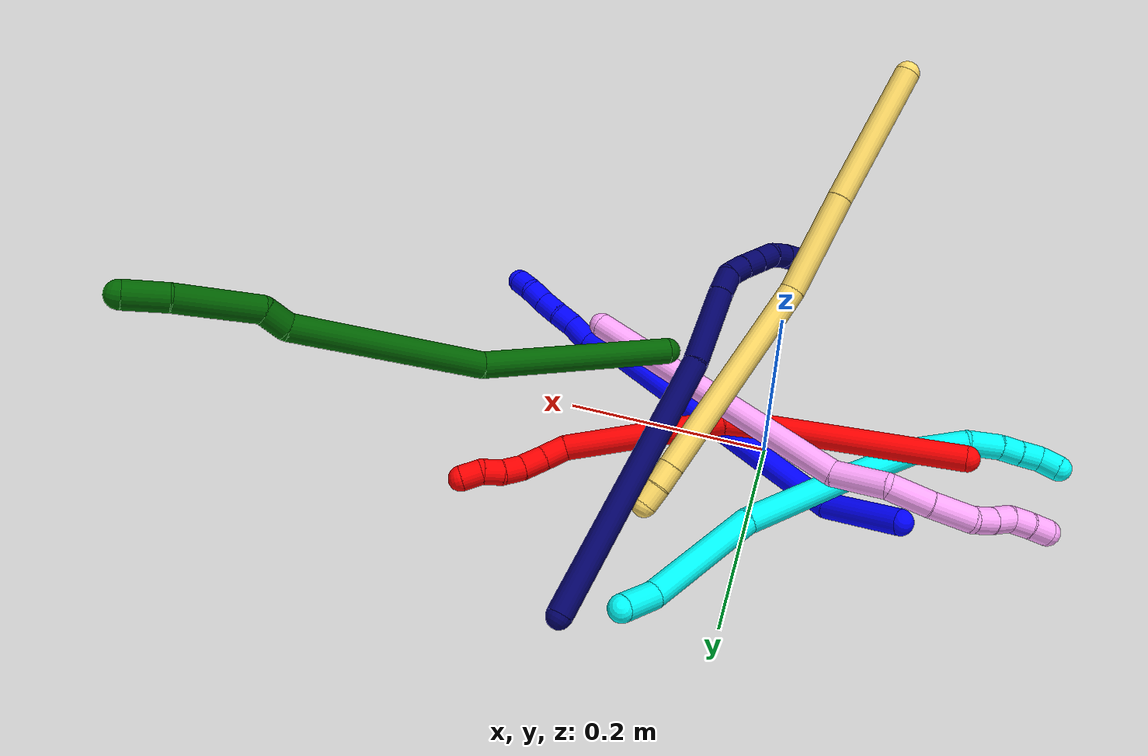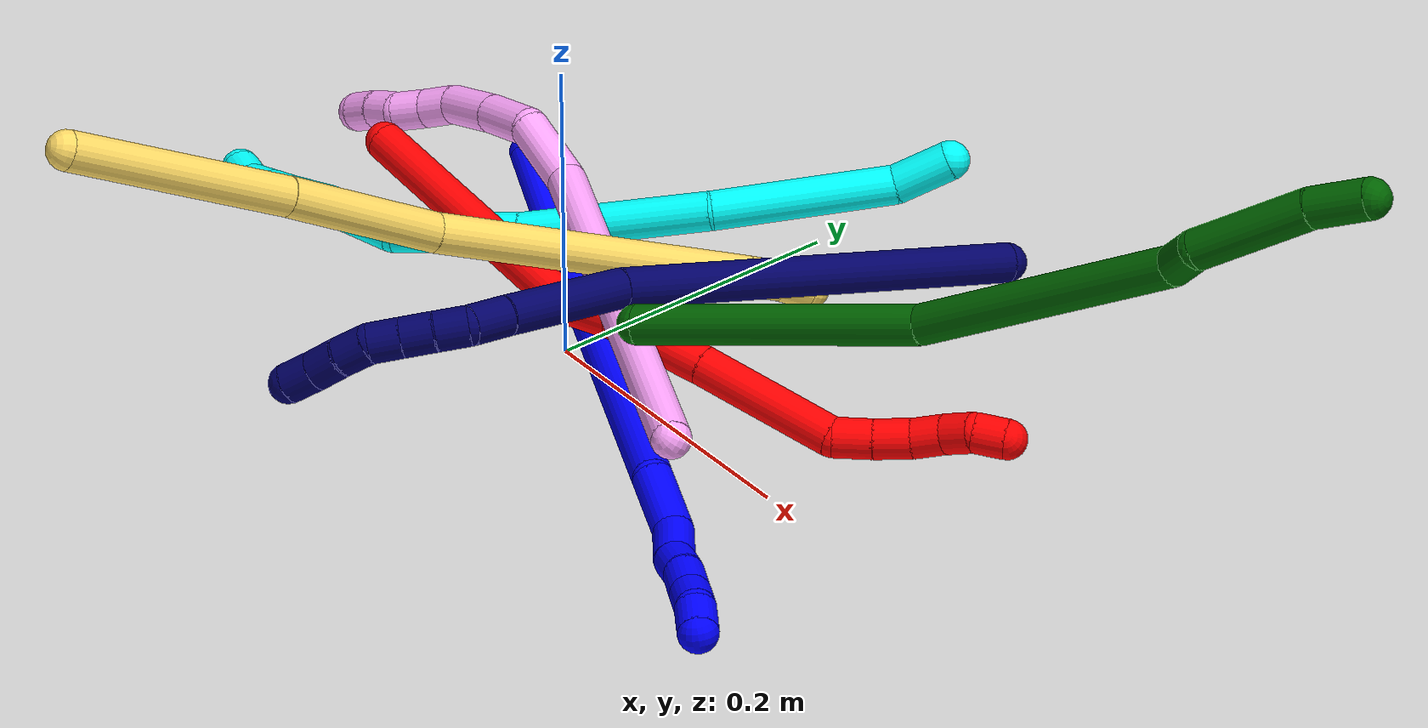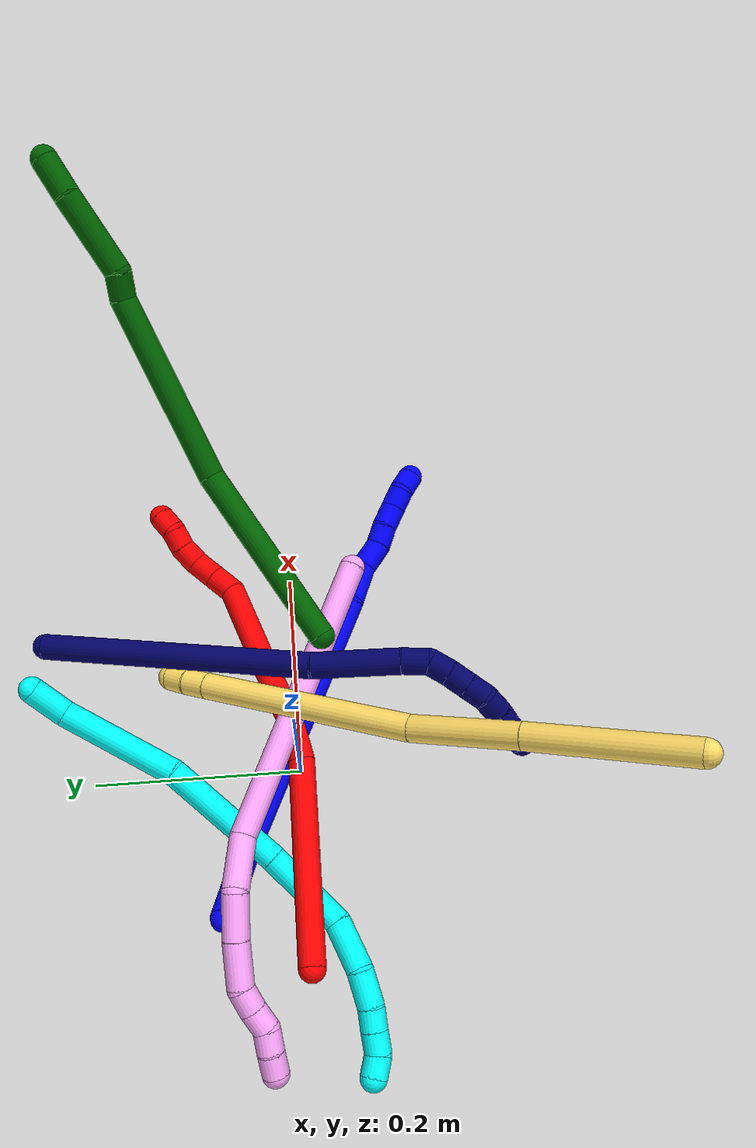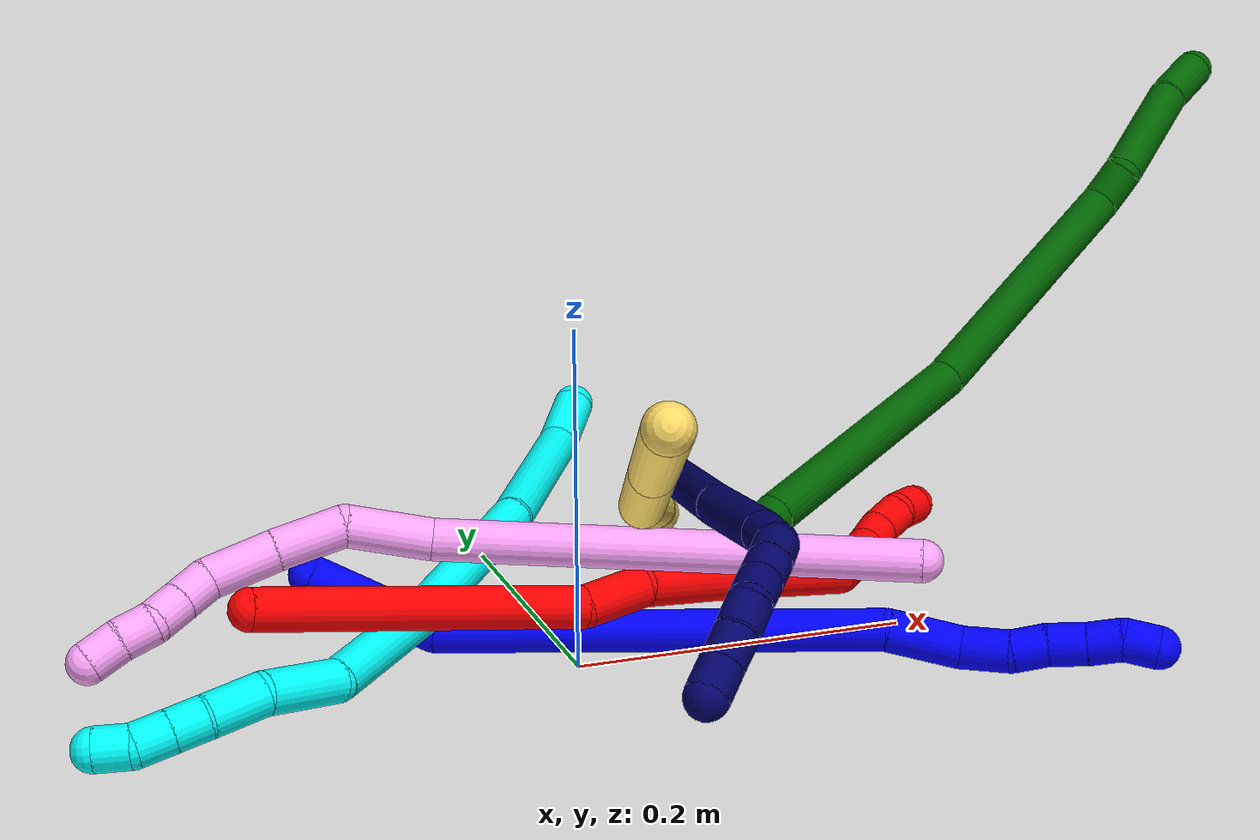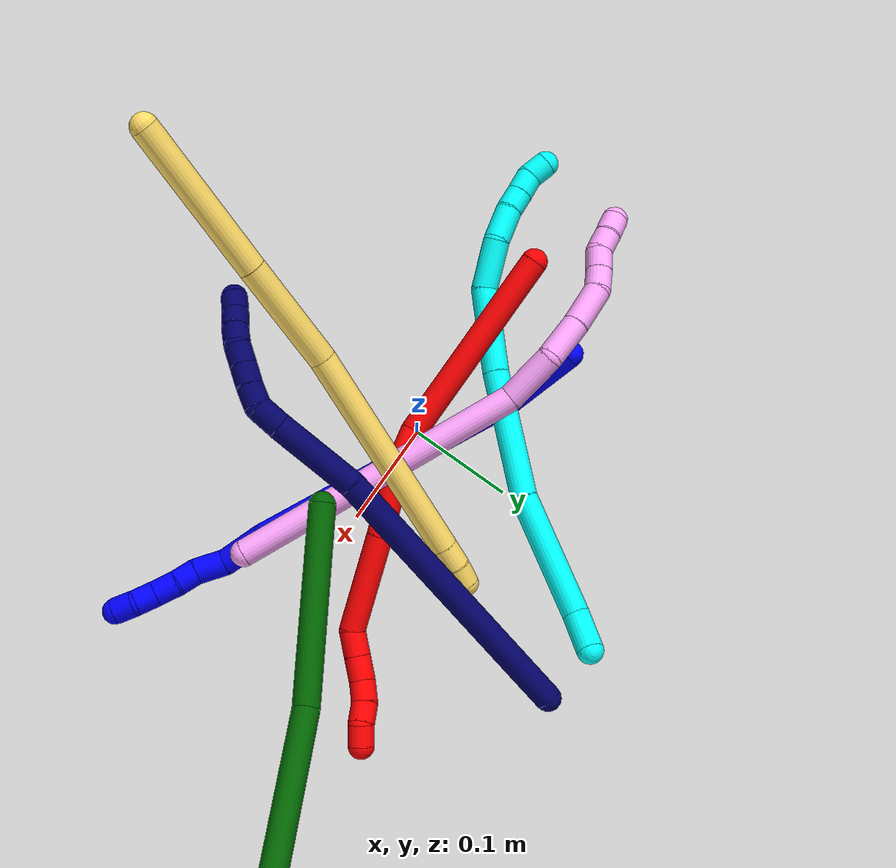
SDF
<sdf version="1.7">
 <world name="default">
  <plugin name="TubeGeneratorPlugin" filename="libtube_generator_plugin.so"/>
  <model name="photoneo_s_sensor">
   <static>1</static>
   <pose>0 0 2 1.57079 1.57079 3.14159</pose>
   <link name="link">
    <inertial><mass>0.1</mass></inertial>
    <sensor name="sensor" type="depth">
     <update_rate>30</update_rate>
     <camera>
      <horizontal_fov>1.22</horizontal_fov>
      <image><width>1920</width><height>1200</height><format>B8G8R8</format></image>
      <clip><near>0.1</near><far>4</far></clip>
      <depth_camera><output>points</output></depth_camera>
     </camera>
     <plugin name="camera_plugin" filename="libgazebo_ros_depth_camera.so">
      <baseline>0.2</baseline>
      <alwaysOn>1</alwaysOn>
      <updateRate>0.0</updateRate>
      <cameraName>camera_ir</cameraName>
      <imageTopicName>/camera/color/image_raw</imageTopicName>
      <cameraInfoTopicName>/camera/color/camera_info</cameraInfoTopicName>
      <depthImageTopicName>/camera/depth/image_raw</depthImageTopicName>
      <depthImageCameraInfoTopicName>/camera/depth/camera_info</depthImageCameraInfoTopicName>
      <pointCloudTopicName>/camera/depth/points</pointCloudTopicName>
      <frameName>fr_optical</frameName>
      <pointCloudCutoff>0.1</pointCloudCutoff>
      <pointCloudCutoffMax>2.0</pointCloudCutoffMax>
      <distortionK1>0</distortionK1>
      <distortionK2>0</distortionK2>
      <distortionK3>0</distortionK3>
      <distortionT1>0</distortionT1>
      <distortionT2>0</distortionT2>
      <CxPrime>0</CxPrime>
      <Cx>0</Cx>
      <Cy>0</Cy>
      <focalLength>0</focalLength>
      <hackBaseline>0</hackBaseline>
     </plugin>
    </sensor>
   </link>
  </model>
  <gravity>0 0 -9.8</gravity>
  <magnetic_field>6e-06 2.3e-05 -4.2e-05</magnetic_field>
  <atmosphere type="adiabatic"/>
  <physics name="default_physics" default="0" type="ode">
   <max_step_size>0.003</max_step_size>
   <real_time_factor>1</real_time_factor>
   <real_time_update_rate>1000</real_time_update_rate>
   <max_contacts>10000</max_contacts>
   <ode>
    <solver>
     <type>quick</type>
     <iters>100</iters>
     <sor>1.3</sor>
     <use_dynamic_moi_rescaling>0</use_dynamic_moi_rescaling>
    </solver>
    <constraints>
     <contact_max_correcting_vel>0</contact_max_correcting_vel>
     <contact_surface_layer>0.001</contact_surface_layer>
     <cfm>0</cfm>
     <erp>0.2</erp>
    </constraints>
   </ode>
  </physics>
  <scene><ambient>0.4 0.4 0.4 1</ambient><background>0.7 0.7 0.7 1</background><shadows>0</shadows></scene>
  <audio><device>default</device></audio>
  <spherical_coordinates>
   <surface_model>EARTH_WGS84</surface_model>
   <latitude_deg>0</latitude_deg>
   <longitude_deg>0</longitude_deg>
   <elevation>0</elevation>
   <heading_deg>0</heading_deg>
  </spherical_coordinates>
  <model name="bin">
   <static>1</static>
   <link name="bottom">
    <collision name="collision-bottom">
     <pose>0 0 -0.01 0 -0 0</pose>
     <geometry><box><size>0.8 0.6 0.02</size></box></geometry>
     <surface>
      <friction><ode><mu>100</mu><mu2>100</mu2></ode></friction>
      <contact><collide_bitmask>65535</collide_bitmask></contact>
     </surface>
    </collision>
   </link>
   <link name="west_wall">
    <collision name="collision-west_wall">
     <pose>-0.41 0 0.1 0 -0 0</pose>
     <geometry><box><size>0.02 0.6 0.2</size></box></geometry>
     <surface>
      <friction><ode><mu>100</mu><mu2>100</mu2></ode></friction>
      <contact><collide_bitmask>65535</collide_bitmask></contact>
     </surface>
    </collision>
   </link>
   <link name="east_wall">
    <collision name="collision-east_wall">
     <pose>0.41 0 0.1 0 -0 0</pose>
     <geometry><box><size>0.02 0.6 0.2</size></box></geometry>
     <surface>
      <friction><ode><mu>100</mu><mu2>100</mu2></ode></friction>
      <contact><collide_bitmask>65535</collide_bitmask></contact>
     </surface>
    </collision>
   </link>
   <link name="south_wall">
    <collision name="collision-south_wall">
     <pose>0 -0.31 0.1 0 -0 0</pose>
     <geometry><box><size>0.8 0.02 0.2</size></box></geometry>
     <surface>
      <friction><ode><mu>100</mu><mu2>100</mu2></ode></friction>
      <contact><collide_bitmask>65535</collide_bitmask></contact>
     </surface>
    </collision>
   </link>
   <link name="north_wall">
    <collision name="collision-north_wall">
     <pose>0 0.31 0.1 0 -0 0</pose>
     <geometry><box><size>0.8 0.02 0.2</size></box></geometry>
     <surface>
      <friction><ode><mu>100</mu><mu2>100</mu2></ode></friction>
      <contact><collide_bitmask>65535</collide_bitmask></contact>
     </surface>
    </collision>
   </link>
  </model>
  <model name="1">
   <static>0</static>
   <link name="1">
    <collision name="collision-cylinder-e_1_1_4">
     <pose>0.028472 -0.011102 -0.025605 2.73249 0.7954 2.22417</pose>
     <geometry><cylinder><radius>0.0125</radius><length>0.079738</length></cylinder></geometry>
     <surface>
      <friction><ode><mu>1.16</mu><mu2>1.16</mu2><slip1>0</slip1><slip2>0</slip2></ode></friction>
      <contact><ode><kp>1e+06</kp><kd>1</kd><max_vel>0</max_vel><min_depth>0.001</min_depth></ode></contact>
     </surface>
    </collision>
    <visual name="visual-cylinder-e_1_1_4">
     <pose>0.028472 -0.011102 -0.025605 2.73249 0.7954 2.22417</pose>
     <geometry><cylinder><radius>0.0125</radius><length>0.079738</length></cylinder></geometry>
     <material><ambient>0 0 1 1</ambient></material>
    </visual>
    <collision name="collision-cylinder-e_2_4_5">
     <pose>0.171823 -0.080918 -0.075096 1.95716 1.06659 1.44048</pose>
     <geometry><cylinder><radius>0.0125</radius><length>0.262411</length></cylinder></geometry>
     <surface>
      <friction><ode><mu>1.16</mu><mu2>1.16</mu2><slip1>0</slip1><slip2>0</slip2></ode></friction>
      <contact><ode><kp>1e+06</kp><kd>1</kd><max_vel>0</max_vel><min_depth>0.001</min_depth></ode></contact>
     </surface>
    </collision>
    <visual name="visual-cylinder-e_2_4_5">
     <pose>0.171823 -0.080918 -0.075096 1.95716 1.06659 1.44048</pose>
     <geometry><cylinder><radius>0.0125</radius><length>0.262411</length></cylinder></geometry>
     <material><ambient>0 0 1 1</ambient></material>
    </visual>
    <collision name="collision-cylinder-e_3_5_6">
     <pose>0.304836 -0.147415 -0.109065 2.48422 0.958458 1.97995</pose>
     <geometry><cylinder><radius>0.0125</radius><length>0.044323</length></cylinder></geometry>
     <surface>
      <friction><ode><mu>1.16</mu><mu2>1.16</mu2><slip1>0</slip1><slip2>0</slip2></ode></friction>
      <contact><ode><kp>1e+06</kp><kd>1</kd><max_vel>0</max_vel><min_depth>0.001</min_depth></ode></contact>
     </surface>
    </collision>
    <visual name="visual-cylinder-e_3_5_6">
     <pose>0.304836 -0.147415 -0.109065 2.48422 0.958458 1.97995</pose>
     <geometry><cylinder><radius>0.0125</radius><length>0.044323</length></cylinder></geometry>
     <material><ambient>0 0 1 1</ambient></material>
    </visual>
    <collision name="collision-cylinder-e_4_6_7">
     <pose>0.334343 -0.164205 -0.121771 1.85416 0.88107 1.12193</pose>
     <geometry><cylinder><radius>0.0125</radius><length>0.029482</length></cylinder></geometry>
     <surface>
      <friction><ode><mu>1.16</mu><mu2>1.16</mu2><slip1>0</slip1><slip2>0</slip2></ode></friction>
      <contact><ode><kp>1e+06</kp><kd>1</kd><max_vel>0</max_vel><min_depth>0.001</min_depth></ode></contact>
     </surface>
    </collision>
    <visual name="visual-cylinder-e_4_6_7">
     <pose>0.334343 -0.164205 -0.121771 1.85416 0.88107 1.12193</pose>
     <geometry><cylinder><radius>0.0125</radius><length>0.029482</length></cylinder></geometry>
     <material><ambient>0 0 1 1</ambient></material>
    </visual>
    <collision name="collision-cylinder-e_5_7_8">
     <pose>0.355304 -0.177204 -0.124596 1.6213 1.17583 1.2229</pose>
     <geometry><cylinder><radius>0.0125</radius><length>0.020779</length></cylinder></geometry>
     <surface>
      <friction><ode><mu>1.16</mu><mu2>1.16</mu2><slip1>0</slip1><slip2>0</slip2></ode></friction>
      <contact><ode><kp>1e+06</kp><kd>1</kd><max_vel>0</max_vel><min_depth>0.001</min_depth></ode></contact>
     </surface>
    </collision>
    <visual name="visual-cylinder-e_5_7_8">
     <pose>0.355304 -0.177204 -0.124596 1.6213 1.17583 1.2229</pose>
     <geometry><cylinder><radius>0.0125</radius><length>0.020779</length></cylinder></geometry>
     <material><ambient>0 0 1 1</ambient></material>
    </visual>
    <collision name="collision-cylinder-e_6_8_9">
     <pose>0.374611 -0.18667 -0.126417 1.85838 1.03967 1.3075</pose>
     <geometry><cylinder><radius>0.0125</radius><length>0.022541</length></cylinder></geometry>
     <surface>
      <friction><ode><mu>1.16</mu><mu2>1.16</mu2><slip1>0</slip1><slip2>0</slip2></ode></friction>
      <contact><ode><kp>1e+06</kp><kd>1</kd><max_vel>0</max_vel><min_depth>0.001</min_depth></ode></contact>
     </surface>
    </collision>
    <visual name="visual-cylinder-e_6_8_9">
     <pose>0.374611 -0.18667 -0.126417 1.85838 1.03967 1.3075</pose>
     <geometry><cylinder><radius>0.0125</radius><length>0.022541</length></cylinder></geometry>
     <material><ambient>0 0 1 1</ambient></material>
    </visual>
    <collision name="collision-cylinder-e_7_9_10">
     <pose>0.393242 -0.19724 -0.128309 1.62428 1.05084 1.09789</pose>
     <geometry><cylinder><radius>0.0125</radius><length>0.020541</length></cylinder></geometry>
     <surface>
      <friction><ode><mu>1.16</mu><mu2>1.16</mu2><slip1>0</slip1><slip2>0</slip2></ode></friction>
      <contact><ode><kp>1e+06</kp><kd>1</kd><max_vel>0</max_vel><min_depth>0.001</min_depth></ode></contact>
     </surface>
    </collision>
    <visual name="visual-cylinder-e_7_9_10">
     <pose>0.393242 -0.19724 -0.128309 1.62428 1.05084 1.09789</pose>
     <geometry><cylinder><radius>0.0125</radius><length>0.020541</length></cylinder></geometry>
     <material><ambient>0 0 1 1</ambient></material>
    </visual>
    <collision name="collision-cylinder-e_8_10_2">
     <pose>0.409784 -0.207872 -0.132187 2.14798 0.857081 1.40043</pose>
     <geometry><cylinder><radius>0.0125</radius><length>0.020184</length></cylinder></geometry>
     <surface>
      <friction><ode><mu>1.16</mu><mu2>1.16</mu2><slip1>0</slip1><slip2>0</slip2></ode></friction>
      <contact><ode><kp>1e+06</kp><kd>1</kd><max_vel>0</max_vel><min_depth>0.001</min_depth></ode></contact>
     </surface>
    </collision>
    <visual name="visual-cylinder-e_8_10_2">
     <pose>0.409784 -0.207872 -0.132187 2.14798 0.857081 1.40043</pose>
     <geometry><cylinder><radius>0.0125</radius><length>0.020184</length></cylinder></geometry>
     <material><ambient>0 0 1 1</ambient></material>
    </visual>
    <collision name="collision-sphere-2">
     <pose>0.417413 -0.213408 -0.135792 0 -0 0</pose>
     <geometry><sphere><radius>0.0125</radius></sphere></geometry>
     <surface>
      <friction><ode><mu>1.16</mu><mu2>1.16</mu2><slip1>0</slip1><slip2>0</slip2></ode></friction>
      <contact><ode><kp>1e+06</kp><kd>1</kd><max_vel>0</max_vel><min_depth>0.001</min_depth></ode></contact>
     </surface>
    </collision>
    <visual name="visual-sphere-2">
     <pose>0.417413 -0.213408 -0.135792 0 -0 0</pose>
     <geometry><sphere><radius>0.0125</radius></sphere></geometry>
     <material><ambient>0 0 1 1</ambient></material>
    </visual>
    <collision name="collision-sphere-10">
     <pose>0.402155 -0.202335 -0.128581 0 -0 0</pose>
     <geometry><sphere><radius>0.0125</radius></sphere></geometry>
     <surface>
      <friction><ode><mu>1.16</mu><mu2>1.16</mu2><slip1>0</slip1><slip2>0</slip2></ode></friction>
      <contact><ode><kp>1e+06</kp><kd>1</kd><max_vel>0</max_vel><min_depth>0.001</min_depth></ode></contact>
     </surface>
    </collision>
    <visual name="visual-sphere-10">
     <pose>0.402155 -0.202335 -0.128581 0 -0 0</pose>
     <geometry><sphere><radius>0.0125</radius></sphere></geometry>
     <material><ambient>0 0 1 1</ambient></material>
    </visual>
    <collision name="collision-sphere-9">
     <pose>0.384329 -0.192144 -0.128036 0 -0 0</pose>
     <geometry><sphere><radius>0.0125</radius></sphere></geometry>
     <surface>
      <friction><ode><mu>1.16</mu><mu2>1.16</mu2><slip1>0</slip1><slip2>0</slip2></ode></friction>
      <contact><ode><kp>1e+06</kp><kd>1</kd><max_vel>0</max_vel><min_depth>0.001</min_depth></ode></contact>
     </surface>
    </collision>
    <visual name="visual-sphere-9">
     <pose>0.384329 -0.192144 -0.128036 0 -0 0</pose>
     <geometry><sphere><radius>0.0125</radius></sphere></geometry>
     <material><ambient>0 0 1 1</ambient></material>
    </visual>
    <collision name="collision-sphere-4">
     <pose>0.056945 -0.022203 -0.051211 0 -0 0</pose>
     <geometry><sphere><radius>0.0125</radius></sphere></geometry>
     <surface>
      <friction><ode><mu>1.16</mu><mu2>1.16</mu2><slip1>0</slip1><slip2>0</slip2></ode></friction>
      <contact><ode><kp>1e+06</kp><kd>1</kd><max_vel>0</max_vel><min_depth>0.001</min_depth></ode></contact>
     </surface>
    </collision>
    <visual name="visual-sphere-4">
     <pose>0.056945 -0.022203 -0.051211 0 -0 0</pose>
     <geometry><sphere><radius>0.0125</radius></sphere></geometry>
     <material><ambient>0 0 1 1</ambient></material>
    </visual>
    <collision name="collision-sphere-1">
     <geometry><sphere><radius>0.0125</radius></sphere></geometry>
     <surface>
      <friction><ode><mu>1.16</mu><mu2>1.16</mu2><slip1>0</slip1><slip2>0</slip2></ode></friction>
      <contact><ode><kp>1e+06</kp><kd>1</kd><max_vel>0</max_vel><min_depth>0.001</min_depth></ode></contact>
     </surface>
    </collision>
    <visual name="visual-sphere-1">
     <geometry><sphere><radius>0.0125</radius></sphere></geometry>
     <material><ambient>0 0 1 1</ambient></material>
    </visual>
    <collision name="collision-sphere-8">
     <pose>0.364893 -0.181196 -0.124798 0 -0 0</pose>
     <geometry><sphere><radius>0.0125</radius></sphere></geometry>
     <surface>
      <friction><ode><mu>1.16</mu><mu2>1.16</mu2><slip1>0</slip1><slip2>0</slip2></ode></friction>
      <contact><ode><kp>1e+06</kp><kd>1</kd><max_vel>0</max_vel><min_depth>0.001</min_depth></ode></contact>
     </surface>
    </collision>
    <visual name="visual-sphere-8">
     <pose>0.364893 -0.181196 -0.124798 0 -0 0</pose>
     <geometry><sphere><radius>0.0125</radius></sphere></geometry>
     <material><ambient>0 0 1 1</ambient></material>
    </visual>
    <collision name="collision-sphere-5">
     <pose>0.286701 -0.139632 -0.098982 0 -0 0</pose>
     <geometry><sphere><radius>0.0125</radius></sphere></geometry>
     <surface>
      <friction><ode><mu>1.16</mu><mu2>1.16</mu2><slip1>0</slip1><slip2>0</slip2></ode></friction>
      <contact><ode><kp>1e+06</kp><kd>1</kd><max_vel>0</max_vel><min_depth>0.001</min_depth></ode></contact>
     </surface>
    </collision>
    <visual name="visual-sphere-5">
     <pose>0.286701 -0.139632 -0.098982 0 -0 0</pose>
     <geometry><sphere><radius>0.0125</radius></sphere></geometry>
     <material><ambient>0 0 1 1</ambient></material>
    </visual>
    <collision name="collision-sphere-6">
     <pose>0.322971 -0.155199 -0.119149 0 -0 0</pose>
     <geometry><sphere><radius>0.0125</radius></sphere></geometry>
     <surface>
      <friction><ode><mu>1.16</mu><mu2>1.16</mu2><slip1>0</slip1><slip2>0</slip2></ode></friction>
      <contact><ode><kp>1e+06</kp><kd>1</kd><max_vel>0</max_vel><min_depth>0.001</min_depth></ode></contact>
     </surface>
    </collision>
    <visual name="visual-sphere-6">
     <pose>0.322971 -0.155199 -0.119149 0 -0 0</pose>
     <geometry><sphere><radius>0.0125</radius></sphere></geometry>
     <material><ambient>0 0 1 1</ambient></material>
    </visual>
    <collision name="collision-sphere-7">
     <pose>0.345714 -0.173211 -0.124394 0 -0 0</pose>
     <geometry><sphere><radius>0.0125</radius></sphere></geometry>
     <surface>
      <friction><ode><mu>1.16</mu><mu2>1.16</mu2><slip1>0</slip1><slip2>0</slip2></ode></friction>
      <contact><ode><kp>1e+06</kp><kd>1</kd><max_vel>0</max_vel><min_depth>0.001</min_depth></ode></contact>
     </surface>
    </collision>
    <visual name="visual-sphere-7">
     <pose>0.345714 -0.173211 -0.124394 0 -0 0</pose>
     <geometry><sphere><radius>0.0125</radius></sphere></geometry>
     <material><ambient>0 0 1 1</ambient></material>
    </visual>
    <inertial>
     <pose>0.205805 -0.099262 -0.081828 0 -0 0</pose>
     <mass>0.5</mass>
     <inertia>
      <ixx>0.000869</ixx>
      <ixy>0</ixy>
      <ixz>0</ixz>
      <iyy>0.001938</iyy>
      <iyz>0</iyz>
      <izz>-0.000686</izz>
     </inertia>
    </inertial>
   </link>
   <pose>-0.138043 0.07645 0.047238 -0.023539 -0.238934 0.01699</pose>
  </model>
  <model name="2">
   <static>0</static>
   <link name="2">
    <collision name="collision-cylinder-e_1_1_4">
     <pose>0.071685 0.05326 0.035582 -0.981817 0.841573 -0.469619</pose>
     <geometry><cylinder><radius>0.0125</radius><length>0.192265</length></cylinder></geometry>
     <surface>
      <friction><ode><mu>1.16</mu><mu2>1.16</mu2><slip1>0</slip1><slip2>0</slip2></ode></friction>
      <contact><ode><kp>1e+06</kp><kd>1</kd><max_vel>0</max_vel><min_depth>0.001</min_depth></ode></contact>
     </surface>
    </collision>
    <visual name="visual-cylinder-e_1_1_4">
     <pose>0.071685 0.05326 0.035582 -0.981817 0.841573 -0.469619</pose>
     <geometry><cylinder><radius>0.0125</radius><length>0.192265</length></cylinder></geometry>
     <material><ambient>1 0 0 1</ambient></material>
    </visual>
    <collision name="collision-cylinder-e_2_4_5">
     <pose>0.153118 0.121553 0.079351 -1.07207 0.517633 -0.312002</pose>
     <geometry><cylinder><radius>0.0125</radius><length>0.039398</length></cylinder></geometry>
     <surface>
      <friction><ode><mu>1.16</mu><mu2>1.16</mu2><slip1>0</slip1><slip2>0</slip2></ode></friction>
      <contact><ode><kp>1e+06</kp><kd>1</kd><max_vel>0</max_vel><min_depth>0.001</min_depth></ode></contact>
     </surface>
    </collision>
    <visual name="visual-cylinder-e_2_4_5">
     <pose>0.153118 0.121553 0.079351 -1.07207 0.517633 -0.312002</pose>
     <geometry><cylinder><radius>0.0125</radius><length>0.039398</length></cylinder></geometry>
     <material><ambient>1 0 0 1</ambient></material>
    </visual>
    <collision name="collision-cylinder-e_3_5_6">
     <pose>0.182915 0.161423 0.091153 -1.42633 0.674034 -0.588594</pose>
     <geometry><cylinder><radius>0.0125</radius><length>0.064246</length></cylinder></geometry>
     <surface>
      <friction><ode><mu>1.16</mu><mu2>1.16</mu2><slip1>0</slip1><slip2>0</slip2></ode></friction>
      <contact><ode><kp>1e+06</kp><kd>1</kd><max_vel>0</max_vel><min_depth>0.001</min_depth></ode></contact>
     </surface>
    </collision>
    <visual name="visual-cylinder-e_3_5_6">
     <pose>0.182915 0.161423 0.091153 -1.42633 0.674034 -0.588594</pose>
     <geometry><cylinder><radius>0.0125</radius><length>0.064246</length></cylinder></geometry>
     <material><ambient>1 0 0 1</ambient></material>
    </visual>
    <collision name="collision-cylinder-e_4_6_7">
     <pose>0.233509 0.22184 0.100362 -1.41479 0.70335 -0.608003</pose>
     <geometry><cylinder><radius>0.0125</radius><length>0.094451</length></cylinder></geometry>
     <surface>
      <friction><ode><mu>1.16</mu><mu2>1.16</mu2><slip1>0</slip1><slip2>0</slip2></ode></friction>
      <contact><ode><kp>1e+06</kp><kd>1</kd><max_vel>0</max_vel><min_depth>0.001</min_depth></ode></contact>
     </surface>
    </collision>
    <visual name="visual-cylinder-e_4_6_7">
     <pose>0.233509 0.22184 0.100362 -1.41479 0.70335 -0.608003</pose>
     <geometry><cylinder><radius>0.0125</radius><length>0.094451</length></cylinder></geometry>
     <material><ambient>1 0 0 1</ambient></material>
    </visual>
    <collision name="collision-cylinder-e_5_7_8">
     <pose>0.266793 0.269417 0.105047 -1.64659 0.223932 -0.241418</pose>
     <geometry><cylinder><radius>0.0125</radius><length>0.024679</length></cylinder></geometry>
     <surface>
      <friction><ode><mu>1.16</mu><mu2>1.16</mu2><slip1>0</slip1><slip2>0</slip2></ode></friction>
      <contact><ode><kp>1e+06</kp><kd>1</kd><max_vel>0</max_vel><min_depth>0.001</min_depth></ode></contact>
     </surface>
    </collision>
    <visual name="visual-cylinder-e_5_7_8">
     <pose>0.266793 0.269417 0.105047 -1.64659 0.223932 -0.241418</pose>
     <geometry><cylinder><radius>0.0125</radius><length>0.024679</length></cylinder></geometry>
     <material><ambient>1 0 0 1</ambient></material>
    </visual>
    <collision name="collision-cylinder-e_6_8_9">
     <pose>0.271565 0.293204 0.103732 -1.60508 0.170563 -0.176484</pose>
     <geometry><cylinder><radius>0.0125</radius><length>0.02394</length></cylinder></geometry>
     <surface>
      <friction><ode><mu>1.16</mu><mu2>1.16</mu2><slip1>0</slip1><slip2>0</slip2></ode></friction>
      <contact><ode><kp>1e+06</kp><kd>1</kd><max_vel>0</max_vel><min_depth>0.001</min_depth></ode></contact>
     </surface>
    </collision>
    <visual name="visual-cylinder-e_6_8_9">
     <pose>0.271565 0.293204 0.103732 -1.60508 0.170563 -0.176484</pose>
     <geometry><cylinder><radius>0.0125</radius><length>0.02394</length></cylinder></geometry>
     <material><ambient>1 0 0 1</ambient></material>
    </visual>
    <collision name="collision-cylinder-e_7_9_10">
     <pose>0.274535 0.315097 0.105074 -1.39961 0.091206 -0.076807</pose>
     <geometry><cylinder><radius>0.0125</radius><length>0.020593</length></cylinder></geometry>
     <surface>
      <friction><ode><mu>1.16</mu><mu2>1.16</mu2><slip1>0</slip1><slip2>0</slip2></ode></friction>
      <contact><ode><kp>1e+06</kp><kd>1</kd><max_vel>0</max_vel><min_depth>0.001</min_depth></ode></contact>
     </surface>
    </collision>
    <visual name="visual-cylinder-e_7_9_10">
     <pose>0.274535 0.315097 0.105074 -1.39961 0.091206 -0.076807</pose>
     <geometry><cylinder><radius>0.0125</radius><length>0.020593</length></cylinder></geometry>
     <material><ambient>1 0 0 1</ambient></material>
    </visual>
    <collision name="collision-cylinder-e_8_10_11">
     <pose>0.277492 0.334171 0.11083 -1.15054 0.202705 -0.131701</pose>
     <geometry><cylinder><radius>0.0125</radius><length>0.020061</length></cylinder></geometry>
     <surface>
      <friction><ode><mu>1.16</mu><mu2>1.16</mu2><slip1>0</slip1><slip2>0</slip2></ode></friction>
      <contact><ode><kp>1e+06</kp><kd>1</kd><max_vel>0</max_vel><min_depth>0.001</min_depth></ode></contact>
     </surface>
    </collision>
    <visual name="visual-cylinder-e_8_10_11">
     <pose>0.277492 0.334171 0.11083 -1.15054 0.202705 -0.131701</pose>
     <geometry><cylinder><radius>0.0125</radius><length>0.020061</length></cylinder></geometry>
     <material><ambient>1 0 0 1</ambient></material>
    </visual>
    <collision name="collision-cylinder-e_9_11_2">
     <pose>0.283487 0.352514 0.11505 -1.54824 0.401159 -0.392442</pose>
     <geometry><cylinder><radius>0.0125</radius><length>0.020366</length></cylinder></geometry>
     <surface>
      <friction><ode><mu>1.16</mu><mu2>1.16</mu2><slip1>0</slip1><slip2>0</slip2></ode></friction>
      <contact><ode><kp>1e+06</kp><kd>1</kd><max_vel>0</max_vel><min_depth>0.001</min_depth></ode></contact>
     </surface>
    </collision>
    <visual name="visual-cylinder-e_9_11_2">
     <pose>0.283487 0.352514 0.11505 -1.54824 0.401159 -0.392442</pose>
     <geometry><cylinder><radius>0.0125</radius><length>0.020366</length></cylinder></geometry>
     <material><ambient>1 0 0 1</ambient></material>
    </visual>
    <collision name="collision-sphere-2">
     <pose>0.287464 0.361886 0.115261 0 -0 0</pose>
     <geometry><sphere><radius>0.0125</radius></sphere></geometry>
     <surface>
      <friction><ode><mu>1.16</mu><mu2>1.16</mu2><slip1>0</slip1><slip2>0</slip2></ode></friction>
      <contact><ode><kp>1e+06</kp><kd>1</kd><max_vel>0</max_vel><min_depth>0.001</min_depth></ode></contact>
     </surface>
    </collision>
    <visual name="visual-sphere-2">
     <pose>0.287464 0.361886 0.115261 0 -0 0</pose>
     <geometry><sphere><radius>0.0125</radius></sphere></geometry>
     <material><ambient>1 0 0 1</ambient></material>
    </visual>
    <collision name="collision-sphere-11">
     <pose>0.279511 0.343141 0.114838 0 -0 0</pose>
     <geometry><sphere><radius>0.0125</radius></sphere></geometry>
     <surface>
      <friction><ode><mu>1.16</mu><mu2>1.16</mu2><slip1>0</slip1><slip2>0</slip2></ode></friction>
      <contact><ode><kp>1e+06</kp><kd>1</kd><max_vel>0</max_vel><min_depth>0.001</min_depth></ode></contact>
     </surface>
    </collision>
    <visual name="visual-sphere-11">
     <pose>0.279511 0.343141 0.114838 0 -0 0</pose>
     <geometry><sphere><radius>0.0125</radius></sphere></geometry>
     <material><ambient>1 0 0 1</ambient></material>
    </visual>
    <collision name="collision-sphere-10">
     <pose>0.275472 0.325201 0.106821 0 -0 0</pose>
     <geometry><sphere><radius>0.0125</radius></sphere></geometry>
     <surface>
      <friction><ode><mu>1.16</mu><mu2>1.16</mu2><slip1>0</slip1><slip2>0</slip2></ode></friction>
      <contact><ode><kp>1e+06</kp><kd>1</kd><max_vel>0</max_vel><min_depth>0.001</min_depth></ode></contact>
     </surface>
    </collision>
    <visual name="visual-sphere-10">
     <pose>0.275472 0.325201 0.106821 0 -0 0</pose>
     <geometry><sphere><radius>0.0125</radius></sphere></geometry>
     <material><ambient>1 0 0 1</ambient></material>
    </visual>
    <collision name="collision-sphere-9">
     <pose>0.273597 0.304993 0.103327 0 -0 0</pose>
     <geometry><sphere><radius>0.0125</radius></sphere></geometry>
     <surface>
      <friction><ode><mu>1.16</mu><mu2>1.16</mu2><slip1>0</slip1><slip2>0</slip2></ode></friction>
      <contact><ode><kp>1e+06</kp><kd>1</kd><max_vel>0</max_vel><min_depth>0.001</min_depth></ode></contact>
     </surface>
    </collision>
    <visual name="visual-sphere-9">
     <pose>0.273597 0.304993 0.103327 0 -0 0</pose>
     <geometry><sphere><radius>0.0125</radius></sphere></geometry>
     <material><ambient>1 0 0 1</ambient></material>
    </visual>
    <collision name="collision-sphere-4">
     <pose>0.14337 0.10652 0.071164 0 -0 0</pose>
     <geometry><sphere><radius>0.0125</radius></sphere></geometry>
     <surface>
      <friction><ode><mu>1.16</mu><mu2>1.16</mu2><slip1>0</slip1><slip2>0</slip2></ode></friction>
      <contact><ode><kp>1e+06</kp><kd>1</kd><max_vel>0</max_vel><min_depth>0.001</min_depth></ode></contact>
     </surface>
    </collision>
    <visual name="visual-sphere-4">
     <pose>0.14337 0.10652 0.071164 0 -0 0</pose>
     <geometry><sphere><radius>0.0125</radius></sphere></geometry>
     <material><ambient>1 0 0 1</ambient></material>
    </visual>
    <collision name="collision-sphere-1">
     <geometry><sphere><radius>0.0125</radius></sphere></geometry>
     <surface>
      <friction><ode><mu>1.16</mu><mu2>1.16</mu2><slip1>0</slip1><slip2>0</slip2></ode></friction>
      <contact><ode><kp>1e+06</kp><kd>1</kd><max_vel>0</max_vel><min_depth>0.001</min_depth></ode></contact>
     </surface>
    </collision>
    <visual name="visual-sphere-1">
     <geometry><sphere><radius>0.0125</radius></sphere></geometry>
     <material><ambient>1 0 0 1</ambient></material>
    </visual>
    <collision name="collision-sphere-8">
     <pose>0.269533 0.281414 0.104136 0 -0 0</pose>
     <geometry><sphere><radius>0.0125</radius></sphere></geometry>
     <surface>
      <friction><ode><mu>1.16</mu><mu2>1.16</mu2><slip1>0</slip1><slip2>0</slip2></ode></friction>
      <contact><ode><kp>1e+06</kp><kd>1</kd><max_vel>0</max_vel><min_depth>0.001</min_depth></ode></contact>
     </surface>
    </collision>
    <visual name="visual-sphere-8">
     <pose>0.269533 0.281414 0.104136 0 -0 0</pose>
     <geometry><sphere><radius>0.0125</radius></sphere></geometry>
     <material><ambient>1 0 0 1</ambient></material>
    </visual>
    <collision name="collision-sphere-5">
     <pose>0.162866 0.136586 0.087539 0 -0 0</pose>
     <geometry><sphere><radius>0.0125</radius></sphere></geometry>
     <surface>
      <friction><ode><mu>1.16</mu><mu2>1.16</mu2><slip1>0</slip1><slip2>0</slip2></ode></friction>
      <contact><ode><kp>1e+06</kp><kd>1</kd><max_vel>0</max_vel><min_depth>0.001</min_depth></ode></contact>
     </surface>
    </collision>
    <visual name="visual-sphere-5">
     <pose>0.162866 0.136586 0.087539 0 -0 0</pose>
     <geometry><sphere><radius>0.0125</radius></sphere></geometry>
     <material><ambient>1 0 0 1</ambient></material>
    </visual>
    <collision name="collision-sphere-6">
     <pose>0.202964 0.18626 0.094766 0 -0 0</pose>
     <geometry><sphere><radius>0.0125</radius></sphere></geometry>
     <surface>
      <friction><ode><mu>1.16</mu><mu2>1.16</mu2><slip1>0</slip1><slip2>0</slip2></ode></friction>
      <contact><ode><kp>1e+06</kp><kd>1</kd><max_vel>0</max_vel><min_depth>0.001</min_depth></ode></contact>
     </surface>
    </collision>
    <visual name="visual-sphere-6">
     <pose>0.202964 0.18626 0.094766 0 -0 0</pose>
     <geometry><sphere><radius>0.0125</radius></sphere></geometry>
     <material><ambient>1 0 0 1</ambient></material>
    </visual>
    <collision name="collision-sphere-7">
     <pose>0.264053 0.25742 0.105958 0 -0 0</pose>
     <geometry><sphere><radius>0.0125</radius></sphere></geometry>
     <surface>
      <friction><ode><mu>1.16</mu><mu2>1.16</mu2><slip1>0</slip1><slip2>0</slip2></ode></friction>
      <contact><ode><kp>1e+06</kp><kd>1</kd><max_vel>0</max_vel><min_depth>0.001</min_depth></ode></contact>
     </surface>
    </collision>
    <visual name="visual-sphere-7">
     <pose>0.264053 0.25742 0.105958 0 -0 0</pose>
     <geometry><sphere><radius>0.0125</radius></sphere></geometry>
     <material><ambient>1 0 0 1</ambient></material>
    </visual>
    <inertial>
     <pose>0.167402 0.160786 0.074218 0 -0 0</pose>
     <mass>0.5</mass>
     <inertia>
      <ixx>0.000228</ixx>
      <ixy>0</ixy>
      <ixz>0</ixz>
      <iyy>0.000319</iyy>
      <iyz>0</iyz>
      <izz>-0.000927</izz>
     </inertia>
    </inertial>
   </link>
   <pose>-0.187245 1.8e-05 0.060189 0.297423 0.740476 -0.445327</pose>
  </model>
  <model name="3">
   <static>0</static>
   <link name="3">
    <collision name="collision-cylinder-e_1_1_4">
     <pose>-0.015244 0.002353 0.010815 -0.21422 -0.942822 0.109507</pose>
     <geometry><cylinder><radius>0.0125</radius><length>0.037676</length></cylinder></geometry>
     <surface>
      <friction><ode><mu>1.16</mu><mu2>1.16</mu2><slip1>0</slip1><slip2>0</slip2></ode></friction>
      <contact><ode><kp>1e+06</kp><kd>1</kd><max_vel>0</max_vel><min_depth>0.001</min_depth></ode></contact>
     </surface>
    </collision>
    <visual name="visual-cylinder-e_1_1_4">
     <pose>-0.015244 0.002353 0.010815 -0.21422 -0.942822 0.109507</pose>
     <geometry><cylinder><radius>0.0125</radius><length>0.037676</length></cylinder></geometry>
     <material><ambient>0.003922 1 0.996078 1</ambient></material>
    </visual>
    <collision name="collision-cylinder-e_2_4_5">
     <pose>-0.083973 0.022223 0.036439 -0.868935 -1.16564 0.593718</pose>
     <geometry><cylinder><radius>0.0125</radius><length>0.116393</length></cylinder></geometry>
     <surface>
      <friction><ode><mu>1.16</mu><mu2>1.16</mu2><slip1>0</slip1><slip2>0</slip2></ode></friction>
      <contact><ode><kp>1e+06</kp><kd>1</kd><max_vel>0</max_vel><min_depth>0.001</min_depth></ode></contact>
     </surface>
    </collision>
    <visual name="visual-cylinder-e_2_4_5">
     <pose>-0.083973 0.022223 0.036439 -0.868935 -1.16564 0.593718</pose>
     <geometry><cylinder><radius>0.0125</radius><length>0.116393</length></cylinder></geometry>
     <material><ambient>0.003922 1 0.996078 1</ambient></material>
    </visual>
    <collision name="collision-cylinder-e_3_5_6">
     <pose>-0.195268 0.044955 0.069917 -0.27242 -1.2473 0.196574</pose>
     <geometry><cylinder><radius>0.0125</radius><length>0.121946</length></cylinder></geometry>
     <surface>
      <friction><ode><mu>1.16</mu><mu2>1.16</mu2><slip1>0</slip1><slip2>0</slip2></ode></friction>
      <contact><ode><kp>1e+06</kp><kd>1</kd><max_vel>0</max_vel><min_depth>0.001</min_depth></ode></contact>
     </surface>
    </collision>
    <visual name="visual-cylinder-e_3_5_6">
     <pose>-0.195268 0.044955 0.069917 -0.27242 -1.2473 0.196574</pose>
     <geometry><cylinder><radius>0.0125</radius><length>0.121946</length></cylinder></geometry>
     <material><ambient>0.003922 1 0.996078 1</ambient></material>
    </visual>
    <collision name="collision-cylinder-e_4_6_7">
     <pose>-0.293122 0.051406 0.097575 -0.136707 -1.34794 0.109254</pose>
     <geometry><cylinder><radius>0.0125</radius><length>0.082118</length></cylinder></geometry>
     <surface>
      <friction><ode><mu>1.16</mu><mu2>1.16</mu2><slip1>0</slip1><slip2>0</slip2></ode></friction>
      <contact><ode><kp>1e+06</kp><kd>1</kd><max_vel>0</max_vel><min_depth>0.001</min_depth></ode></contact>
     </surface>
    </collision>
    <visual name="visual-cylinder-e_4_6_7">
     <pose>-0.293122 0.051406 0.097575 -0.136707 -1.34794 0.109254</pose>
     <geometry><cylinder><radius>0.0125</radius><length>0.082118</length></cylinder></geometry>
     <material><ambient>0.003922 1 0.996078 1</ambient></material>
    </visual>
    <collision name="collision-cylinder-e_5_7_8">
     <pose>-0.355886 0.046091 0.104663 1.85334 -1.27909 -1.56124</pose>
     <geometry><cylinder><radius>0.0125</radius><length>0.047447</length></cylinder></geometry>
     <surface>
      <friction><ode><mu>1.16</mu><mu2>1.16</mu2><slip1>0</slip1><slip2>0</slip2></ode></friction>
      <contact><ode><kp>1e+06</kp><kd>1</kd><max_vel>0</max_vel><min_depth>0.001</min_depth></ode></contact>
     </surface>
    </collision>
    <visual name="visual-cylinder-e_5_7_8">
     <pose>-0.355886 0.046091 0.104663 1.85334 -1.27909 -1.56124</pose>
     <geometry><cylinder><radius>0.0125</radius><length>0.047447</length></cylinder></geometry>
     <material><ambient>0.003922 1 0.996078 1</ambient></material>
    </visual>
    <collision name="collision-cylinder-e_6_8_9">
     <pose>-0.393099 0.031977 0.105384 1.2369 -1.06613 -0.795015</pose>
     <geometry><cylinder><radius>0.0125</radius><length>0.033111</length></cylinder></geometry>
     <surface>
      <friction><ode><mu>1.16</mu><mu2>1.16</mu2><slip1>0</slip1><slip2>0</slip2></ode></friction>
      <contact><ode><kp>1e+06</kp><kd>1</kd><max_vel>0</max_vel><min_depth>0.001</min_depth></ode></contact>
     </surface>
    </collision>
    <visual name="visual-cylinder-e_6_8_9">
     <pose>-0.393099 0.031977 0.105384 1.2369 -1.06613 -0.795015</pose>
     <geometry><cylinder><radius>0.0125</radius><length>0.033111</length></cylinder></geometry>
     <material><ambient>0.003922 1 0.996078 1</ambient></material>
    </visual>
    <collision name="collision-cylinder-e_7_9_10">
     <pose>-0.41547 0.018361 0.109957 1.25923 -0.891734 -0.670164</pose>
     <geometry><cylinder><radius>0.0125</radius><length>0.020251</length></cylinder></geometry>
     <surface>
      <friction><ode><mu>1.16</mu><mu2>1.16</mu2><slip1>0</slip1><slip2>0</slip2></ode></friction>
      <contact><ode><kp>1e+06</kp><kd>1</kd><max_vel>0</max_vel><min_depth>0.001</min_depth></ode></contact>
     </surface>
    </collision>
    <visual name="visual-cylinder-e_7_9_10">
     <pose>-0.41547 0.018361 0.109957 1.25923 -0.891734 -0.670164</pose>
     <geometry><cylinder><radius>0.0125</radius><length>0.020251</length></cylinder></geometry>
     <material><ambient>0.003922 1 0.996078 1</ambient></material>
    </visual>
    <collision name="collision-cylinder-e_8_10_11">
     <pose>-0.431703 0.006329 0.1138 1.26415 -0.926878 -0.70164</pose>
     <geometry><cylinder><radius>0.0125</radius><length>0.020891</length></cylinder></geometry>
     <surface>
      <friction><ode><mu>1.16</mu><mu2>1.16</mu2><slip1>0</slip1><slip2>0</slip2></ode></friction>
      <contact><ode><kp>1e+06</kp><kd>1</kd><max_vel>0</max_vel><min_depth>0.001</min_depth></ode></contact>
     </surface>
    </collision>
    <visual name="visual-cylinder-e_8_10_11">
     <pose>-0.431703 0.006329 0.1138 1.26415 -0.926878 -0.70164</pose>
     <geometry><cylinder><radius>0.0125</radius><length>0.020891</length></cylinder></geometry>
     <material><ambient>0.003922 1 0.996078 1</ambient></material>
    </visual>
    <collision name="collision-cylinder-e_9_11_2">
     <pose>-0.445879 -0.007862 0.115111 1.6415 -0.615456 -0.657499</pose>
     <geometry><cylinder><radius>0.0125</radius><length>0.020168</length></cylinder></geometry>
     <surface>
      <friction><ode><mu>1.16</mu><mu2>1.16</mu2><slip1>0</slip1><slip2>0</slip2></ode></friction>
      <contact><ode><kp>1e+06</kp><kd>1</kd><max_vel>0</max_vel><min_depth>0.001</min_depth></ode></contact>
     </surface>
    </collision>
    <visual name="visual-cylinder-e_9_11_2">
     <pose>-0.445879 -0.007862 0.115111 1.6415 -0.615456 -0.657499</pose>
     <geometry><cylinder><radius>0.0125</radius><length>0.020168</length></cylinder></geometry>
     <material><ambient>0.003922 1 0.996078 1</ambient></material>
    </visual>
    <collision name="collision-sphere-2">
     <pose>-0.4517 -0.016075 0.114529 0 -0 0</pose>
     <geometry><sphere><radius>0.0125</radius></sphere></geometry>
     <surface>
      <friction><ode><mu>1.16</mu><mu2>1.16</mu2><slip1>0</slip1><slip2>0</slip2></ode></friction>
      <contact><ode><kp>1e+06</kp><kd>1</kd><max_vel>0</max_vel><min_depth>0.001</min_depth></ode></contact>
     </surface>
    </collision>
    <visual name="visual-sphere-2">
     <pose>-0.4517 -0.016075 0.114529 0 -0 0</pose>
     <geometry><sphere><radius>0.0125</radius></sphere></geometry>
     <material><ambient>0.003922 1 0.996078 1</ambient></material>
    </visual>
    <collision name="collision-sphere-11">
     <pose>-0.440057 0.000351 0.115692 0 -0 0</pose>
     <geometry><sphere><radius>0.0125</radius></sphere></geometry>
     <surface>
      <friction><ode><mu>1.16</mu><mu2>1.16</mu2><slip1>0</slip1><slip2>0</slip2></ode></friction>
      <contact><ode><kp>1e+06</kp><kd>1</kd><max_vel>0</max_vel><min_depth>0.001</min_depth></ode></contact>
     </surface>
    </collision>
    <visual name="visual-sphere-11">
     <pose>-0.440057 0.000351 0.115692 0 -0 0</pose>
     <geometry><sphere><radius>0.0125</radius></sphere></geometry>
     <material><ambient>0.003922 1 0.996078 1</ambient></material>
    </visual>
    <collision name="collision-sphere-10">
     <pose>-0.423349 0.012307 0.111907 0 -0 0</pose>
     <geometry><sphere><radius>0.0125</radius></sphere></geometry>
     <surface>
      <friction><ode><mu>1.16</mu><mu2>1.16</mu2><slip1>0</slip1><slip2>0</slip2></ode></friction>
      <contact><ode><kp>1e+06</kp><kd>1</kd><max_vel>0</max_vel><min_depth>0.001</min_depth></ode></contact>
     </surface>
    </collision>
    <visual name="visual-sphere-10">
     <pose>-0.423349 0.012307 0.111907 0 -0 0</pose>
     <geometry><sphere><radius>0.0125</radius></sphere></geometry>
     <material><ambient>0.003922 1 0.996078 1</ambient></material>
    </visual>
    <collision name="collision-sphere-9">
     <pose>-0.407591 0.024414 0.108008 0 -0 0</pose>
     <geometry><sphere><radius>0.0125</radius></sphere></geometry>
     <surface>
      <friction><ode><mu>1.16</mu><mu2>1.16</mu2><slip1>0</slip1><slip2>0</slip2></ode></friction>
      <contact><ode><kp>1e+06</kp><kd>1</kd><max_vel>0</max_vel><min_depth>0.001</min_depth></ode></contact>
     </surface>
    </collision>
    <visual name="visual-sphere-9">
     <pose>-0.407591 0.024414 0.108008 0 -0 0</pose>
     <geometry><sphere><radius>0.0125</radius></sphere></geometry>
     <material><ambient>0.003922 1 0.996078 1</ambient></material>
    </visual>
    <collision name="collision-sphere-4">
     <pose>-0.030488 0.004706 0.021629 0 -0 0</pose>
     <geometry><sphere><radius>0.0125</radius></sphere></geometry>
     <surface>
      <friction><ode><mu>1.16</mu><mu2>1.16</mu2><slip1>0</slip1><slip2>0</slip2></ode></friction>
      <contact><ode><kp>1e+06</kp><kd>1</kd><max_vel>0</max_vel><min_depth>0.001</min_depth></ode></contact>
     </surface>
    </collision>
    <visual name="visual-sphere-4">
     <pose>-0.030488 0.004706 0.021629 0 -0 0</pose>
     <geometry><sphere><radius>0.0125</radius></sphere></geometry>
     <material><ambient>0.003922 1 0.996078 1</ambient></material>
    </visual>
    <collision name="collision-sphere-1">
     <geometry><sphere><radius>0.0125</radius></sphere></geometry>
     <surface>
      <friction><ode><mu>1.16</mu><mu2>1.16</mu2><slip1>0</slip1><slip2>0</slip2></ode></friction>
      <contact><ode><kp>1e+06</kp><kd>1</kd><max_vel>0</max_vel><min_depth>0.001</min_depth></ode></contact>
     </surface>
    </collision>
    <visual name="visual-sphere-1">
     <geometry><sphere><radius>0.0125</radius></sphere></geometry>
     <material><ambient>0.003922 1 0.996078 1</ambient></material>
    </visual>
    <collision name="collision-sphere-8">
     <pose>-0.378608 0.039539 0.102761 0 -0 0</pose>
     <geometry><sphere><radius>0.0125</radius></sphere></geometry>
     <surface>
      <friction><ode><mu>1.16</mu><mu2>1.16</mu2><slip1>0</slip1><slip2>0</slip2></ode></friction>
      <contact><ode><kp>1e+06</kp><kd>1</kd><max_vel>0</max_vel><min_depth>0.001</min_depth></ode></contact>
     </surface>
    </collision>
    <visual name="visual-sphere-8">
     <pose>-0.378608 0.039539 0.102761 0 -0 0</pose>
     <geometry><sphere><radius>0.0125</radius></sphere></geometry>
     <material><ambient>0.003922 1 0.996078 1</ambient></material>
    </visual>
    <collision name="collision-sphere-5">
     <pose>-0.137458 0.03974 0.051249 0 -0 0</pose>
     <geometry><sphere><radius>0.0125</radius></sphere></geometry>
     <surface>
      <friction><ode><mu>1.16</mu><mu2>1.16</mu2><slip1>0</slip1><slip2>0</slip2></ode></friction>
      <contact><ode><kp>1e+06</kp><kd>1</kd><max_vel>0</max_vel><min_depth>0.001</min_depth></ode></contact>
     </surface>
    </collision>
    <visual name="visual-sphere-5">
     <pose>-0.137458 0.03974 0.051249 0 -0 0</pose>
     <geometry><sphere><radius>0.0125</radius></sphere></geometry>
     <material><ambient>0.003922 1 0.996078 1</ambient></material>
    </visual>
    <collision name="collision-sphere-6">
     <pose>-0.253078 0.05017 0.088585 0 -0 0</pose>
     <geometry><sphere><radius>0.0125</radius></sphere></geometry>
     <surface>
      <friction><ode><mu>1.16</mu><mu2>1.16</mu2><slip1>0</slip1><slip2>0</slip2></ode></friction>
      <contact><ode><kp>1e+06</kp><kd>1</kd><max_vel>0</max_vel><min_depth>0.001</min_depth></ode></contact>
     </surface>
    </collision>
    <visual name="visual-sphere-6">
     <pose>-0.253078 0.05017 0.088585 0 -0 0</pose>
     <geometry><sphere><radius>0.0125</radius></sphere></geometry>
     <material><ambient>0.003922 1 0.996078 1</ambient></material>
    </visual>
    <collision name="collision-sphere-7">
     <pose>-0.333165 0.052643 0.106565 0 -0 0</pose>
     <geometry><sphere><radius>0.0125</radius></sphere></geometry>
     <surface>
      <friction><ode><mu>1.16</mu><mu2>1.16</mu2><slip1>0</slip1><slip2>0</slip2></ode></friction>
      <contact><ode><kp>1e+06</kp><kd>1</kd><max_vel>0</max_vel><min_depth>0.001</min_depth></ode></contact>
     </surface>
    </collision>
    <visual name="visual-sphere-7">
     <pose>-0.333165 0.052643 0.106565 0 -0 0</pose>
     <geometry><sphere><radius>0.0125</radius></sphere></geometry>
     <material><ambient>0.003922 1 0.996078 1</ambient></material>
    </visual>
    <inertial>
     <pose>-0.229114 0.031939 0.073137 0 -0 0</pose>
     <mass>0.5</mass>
     <inertia>
      <ixx>0.000111</ixx>
      <ixy>0</ixy>
      <ixz>0</ixz>
      <iyy>0.000386</iyy>
      <iyz>0</iyz>
      <izz>0.000303</izz>
     </inertia>
    </inertial>
   </link>
   <pose>0.076587 0.243336 0.082083 2.92834 0.099369 0.66462</pose>
  </model>
  <model name="4">
   <static>0</static>
   <link name="4">
    <collision name="collision-cylinder-e_1_1_4">
     <pose>-0.09452 0.101769 -0.024459 -1.80667 -0.734504 0.9082</pose>
     <geometry><cylinder><radius>0.0125</radius><length>0.282058</length></cylinder></geometry>
     <surface>
      <friction><ode><mu>1.16</mu><mu2>1.16</mu2><slip1>0</slip1><slip2>0</slip2></ode></friction>
      <contact><ode><kp>1e+06</kp><kd>1</kd><max_vel>0</max_vel><min_depth>0.001</min_depth></ode></contact>
     </surface>
    </collision>
    <visual name="visual-cylinder-e_1_1_4">
     <pose>-0.09452 0.101769 -0.024459 -1.80667 -0.734504 0.9082</pose>
     <geometry><cylinder><radius>0.0125</radius><length>0.282058</length></cylinder></geometry>
     <material><ambient>1 0.65098 0.996078 1</ambient></material>
    </visual>
    <collision name="collision-cylinder-e_2_4_5">
     <pose>-0.206605 0.221839 -0.044742 -1.34644 -0.752145 0.610158</pose>
     <geometry><cylinder><radius>0.0125</radius><length>0.051416</length></cylinder></geometry>
     <surface>
      <friction><ode><mu>1.16</mu><mu2>1.16</mu2><slip1>0</slip1><slip2>0</slip2></ode></friction>
      <contact><ode><kp>1e+06</kp><kd>1</kd><max_vel>0</max_vel><min_depth>0.001</min_depth></ode></contact>
     </surface>
    </collision>
    <visual name="visual-cylinder-e_2_4_5">
     <pose>-0.206605 0.221839 -0.044742 -1.34644 -0.752145 0.610158</pose>
     <geometry><cylinder><radius>0.0125</radius><length>0.051416</length></cylinder></geometry>
     <material><ambient>1 0.65098 0.996078 1</ambient></material>
    </visual>
    <collision name="collision-cylinder-e_3_5_6">
     <pose>-0.243579 0.247411 -0.041986 -1.76376 -1.20624 1.393</pose>
     <geometry><cylinder><radius>0.0125</radius><length>0.041552</length></cylinder></geometry>
     <surface>
      <friction><ode><mu>1.16</mu><mu2>1.16</mu2><slip1>0</slip1><slip2>0</slip2></ode></friction>
      <contact><ode><kp>1e+06</kp><kd>1</kd><max_vel>0</max_vel><min_depth>0.001</min_depth></ode></contact>
     </surface>
    </collision>
    <visual name="visual-cylinder-e_3_5_6">
     <pose>-0.243579 0.247411 -0.041986 -1.76376 -1.20624 1.393</pose>
     <geometry><cylinder><radius>0.0125</radius><length>0.041552</length></cylinder></geometry>
     <material><ambient>1 0.65098 0.996078 1</ambient></material>
    </visual>
    <collision name="collision-cylinder-e_4_6_7">
     <pose>-0.282877 0.260505 -0.043911 -1.65707 -1.28492 1.36871</pose>
     <geometry><cylinder><radius>0.0125</radius><length>0.041456</length></cylinder></geometry>
     <surface>
      <friction><ode><mu>1.16</mu><mu2>1.16</mu2><slip1>0</slip1><slip2>0</slip2></ode></friction>
      <contact><ode><kp>1e+06</kp><kd>1</kd><max_vel>0</max_vel><min_depth>0.001</min_depth></ode></contact>
     </surface>
    </collision>
    <visual name="visual-cylinder-e_4_6_7">
     <pose>-0.282877 0.260505 -0.043911 -1.65707 -1.28492 1.36871</pose>
     <geometry><cylinder><radius>0.0125</radius><length>0.041456</length></cylinder></geometry>
     <material><ambient>1 0.65098 0.996078 1</ambient></material>
    </visual>
    <collision name="collision-cylinder-e_5_7_8">
     <pose>-0.313334 0.265427 -0.042518 0.443632 -1.37476 -0.366142</pose>
     <geometry><cylinder><radius>0.0125</radius><length>0.021554</length></cylinder></geometry>
     <surface>
      <friction><ode><mu>1.16</mu><mu2>1.16</mu2><slip1>0</slip1><slip2>0</slip2></ode></friction>
      <contact><ode><kp>1e+06</kp><kd>1</kd><max_vel>0</max_vel><min_depth>0.001</min_depth></ode></contact>
     </surface>
    </collision>
    <visual name="visual-cylinder-e_5_7_8">
     <pose>-0.313334 0.265427 -0.042518 0.443632 -1.37476 -0.366142</pose>
     <geometry><cylinder><radius>0.0125</radius><length>0.021554</length></cylinder></geometry>
     <material><ambient>1 0.65098 0.996078 1</ambient></material>
    </visual>
    <collision name="collision-cylinder-e_6_8_9">
     <pose>-0.333786 0.263368 -0.037491 0.354156 -1.24498 -0.25546</pose>
     <geometry><cylinder><radius>0.0125</radius><length>0.020859</length></cylinder></geometry>
     <surface>
      <friction><ode><mu>1.16</mu><mu2>1.16</mu2><slip1>0</slip1><slip2>0</slip2></ode></friction>
      <contact><ode><kp>1e+06</kp><kd>1</kd><max_vel>0</max_vel><min_depth>0.001</min_depth></ode></contact>
     </surface>
    </collision>
    <visual name="visual-cylinder-e_6_8_9">
     <pose>-0.333786 0.263368 -0.037491 0.354156 -1.24498 -0.25546</pose>
     <geometry><cylinder><radius>0.0125</radius><length>0.020859</length></cylinder></geometry>
     <material><ambient>1 0.65098 0.996078 1</ambient></material>
    </visual>
    <collision name="collision-cylinder-e_7_9_10">
     <pose>-0.353729 0.264117 -0.034389 -1.58599 -1.38359 1.39854</pose>
     <geometry><cylinder><radius>0.0125</radius><length>0.020484</length></cylinder></geometry>
     <surface>
      <friction><ode><mu>1.16</mu><mu2>1.16</mu2><slip1>0</slip1><slip2>0</slip2></ode></friction>
      <contact><ode><kp>1e+06</kp><kd>1</kd><max_vel>0</max_vel><min_depth>0.001</min_depth></ode></contact>
     </surface>
    </collision>
    <visual name="visual-cylinder-e_7_9_10">
     <pose>-0.353729 0.264117 -0.034389 -1.58599 -1.38359 1.39854</pose>
     <geometry><cylinder><radius>0.0125</radius><length>0.020484</length></cylinder></geometry>
     <material><ambient>1 0.65098 0.996078 1</ambient></material>
    </visual>
    <collision name="collision-cylinder-e_8_10_2">
     <pose>-0.374053 0.266702 -0.035167 -2.40477 -1.47261 2.33627</pose>
     <geometry><cylinder><radius>0.0125</radius><length>0.020621</length></cylinder></geometry>
     <surface>
      <friction><ode><mu>1.16</mu><mu2>1.16</mu2><slip1>0</slip1><slip2>0</slip2></ode></friction>
      <contact><ode><kp>1e+06</kp><kd>1</kd><max_vel>0</max_vel><min_depth>0.001</min_depth></ode></contact>
     </surface>
    </collision>
    <visual name="visual-cylinder-e_8_10_2">
     <pose>-0.374053 0.266702 -0.035167 -2.40477 -1.47261 2.33627</pose>
     <geometry><cylinder><radius>0.0125</radius><length>0.020621</length></cylinder></geometry>
     <material><ambient>1 0.65098 0.996078 1</ambient></material>
    </visual>
    <collision name="collision-sphere-2">
     <pose>-0.384314 0.267381 -0.035915 0 -0 0</pose>
     <geometry><sphere><radius>0.0125</radius></sphere></geometry>
     <surface>
      <friction><ode><mu>1.16</mu><mu2>1.16</mu2><slip1>0</slip1><slip2>0</slip2></ode></friction>
      <contact><ode><kp>1e+06</kp><kd>1</kd><max_vel>0</max_vel><min_depth>0.001</min_depth></ode></contact>
     </surface>
    </collision>
    <visual name="visual-sphere-2">
     <pose>-0.384314 0.267381 -0.035915 0 -0 0</pose>
     <geometry><sphere><radius>0.0125</radius></sphere></geometry>
     <material><ambient>1 0.65098 0.996078 1</ambient></material>
    </visual>
    <collision name="collision-sphere-10">
     <pose>-0.363792 0.266023 -0.034418 0 -0 0</pose>
     <geometry><sphere><radius>0.0125</radius></sphere></geometry>
     <surface>
      <friction><ode><mu>1.16</mu><mu2>1.16</mu2><slip1>0</slip1><slip2>0</slip2></ode></friction>
      <contact><ode><kp>1e+06</kp><kd>1</kd><max_vel>0</max_vel><min_depth>0.001</min_depth></ode></contact>
     </surface>
    </collision>
    <visual name="visual-sphere-10">
     <pose>-0.363792 0.266023 -0.034418 0 -0 0</pose>
     <geometry><sphere><radius>0.0125</radius></sphere></geometry>
     <material><ambient>1 0.65098 0.996078 1</ambient></material>
    </visual>
    <collision name="collision-sphere-9">
     <pose>-0.343666 0.262211 -0.03436 0 -0 0</pose>
     <geometry><sphere><radius>0.0125</radius></sphere></geometry>
     <surface>
      <friction><ode><mu>1.16</mu><mu2>1.16</mu2><slip1>0</slip1><slip2>0</slip2></ode></friction>
      <contact><ode><kp>1e+06</kp><kd>1</kd><max_vel>0</max_vel><min_depth>0.001</min_depth></ode></contact>
     </surface>
    </collision>
    <visual name="visual-sphere-9">
     <pose>-0.343666 0.262211 -0.03436 0 -0 0</pose>
     <geometry><sphere><radius>0.0125</radius></sphere></geometry>
     <material><ambient>1 0.65098 0.996078 1</ambient></material>
    </visual>
    <collision name="collision-sphere-4">
     <pose>-0.189041 0.203537 -0.048919 0 -0 0</pose>
     <geometry><sphere><radius>0.0125</radius></sphere></geometry>
     <surface>
      <friction><ode><mu>1.16</mu><mu2>1.16</mu2><slip1>0</slip1><slip2>0</slip2></ode></friction>
      <contact><ode><kp>1e+06</kp><kd>1</kd><max_vel>0</max_vel><min_depth>0.001</min_depth></ode></contact>
     </surface>
    </collision>
    <visual name="visual-sphere-4">
     <pose>-0.189041 0.203537 -0.048919 0 -0 0</pose>
     <geometry><sphere><radius>0.0125</radius></sphere></geometry>
     <material><ambient>1 0.65098 0.996078 1</ambient></material>
    </visual>
    <collision name="collision-sphere-1">
     <geometry><sphere><radius>0.0125</radius></sphere></geometry>
     <surface>
      <friction><ode><mu>1.16</mu><mu2>1.16</mu2><slip1>0</slip1><slip2>0</slip2></ode></friction>
      <contact><ode><kp>1e+06</kp><kd>1</kd><max_vel>0</max_vel><min_depth>0.001</min_depth></ode></contact>
     </surface>
    </collision>
    <visual name="visual-sphere-1">
     <geometry><sphere><radius>0.0125</radius></sphere></geometry>
     <material><ambient>1 0.65098 0.996078 1</ambient></material>
    </visual>
    <collision name="collision-sphere-8">
     <pose>-0.323905 0.264526 -0.040622 0 -0 0</pose>
     <geometry><sphere><radius>0.0125</radius></sphere></geometry>
     <surface>
      <friction><ode><mu>1.16</mu><mu2>1.16</mu2><slip1>0</slip1><slip2>0</slip2></ode></friction>
      <contact><ode><kp>1e+06</kp><kd>1</kd><max_vel>0</max_vel><min_depth>0.001</min_depth></ode></contact>
     </surface>
    </collision>
    <visual name="visual-sphere-8">
     <pose>-0.323905 0.264526 -0.040622 0 -0 0</pose>
     <geometry><sphere><radius>0.0125</radius></sphere></geometry>
     <material><ambient>1 0.65098 0.996078 1</ambient></material>
    </visual>
    <collision name="collision-sphere-5">
     <pose>-0.224168 0.240141 -0.040566 0 -0 0</pose>
     <geometry><sphere><radius>0.0125</radius></sphere></geometry>
     <surface>
      <friction><ode><mu>1.16</mu><mu2>1.16</mu2><slip1>0</slip1><slip2>0</slip2></ode></friction>
      <contact><ode><kp>1e+06</kp><kd>1</kd><max_vel>0</max_vel><min_depth>0.001</min_depth></ode></contact>
     </surface>
    </collision>
    <visual name="visual-sphere-5">
     <pose>-0.224168 0.240141 -0.040566 0 -0 0</pose>
     <geometry><sphere><radius>0.0125</radius></sphere></geometry>
     <material><ambient>1 0.65098 0.996078 1</ambient></material>
    </visual>
    <collision name="collision-sphere-6">
     <pose>-0.26299 0.254681 -0.043407 0 -0 0</pose>
     <geometry><sphere><radius>0.0125</radius></sphere></geometry>
     <surface>
      <friction><ode><mu>1.16</mu><mu2>1.16</mu2><slip1>0</slip1><slip2>0</slip2></ode></friction>
      <contact><ode><kp>1e+06</kp><kd>1</kd><max_vel>0</max_vel><min_depth>0.001</min_depth></ode></contact>
     </surface>
    </collision>
    <visual name="visual-sphere-6">
     <pose>-0.26299 0.254681 -0.043407 0 -0 0</pose>
     <geometry><sphere><radius>0.0125</radius></sphere></geometry>
     <material><ambient>1 0.65098 0.996078 1</ambient></material>
    </visual>
    <collision name="collision-sphere-7">
     <pose>-0.302764 0.266328 -0.044414 0 -0 0</pose>
     <geometry><sphere><radius>0.0125</radius></sphere></geometry>
     <surface>
      <friction><ode><mu>1.16</mu><mu2>1.16</mu2><slip1>0</slip1><slip2>0</slip2></ode></friction>
      <contact><ode><kp>1e+06</kp><kd>1</kd><max_vel>0</max_vel><min_depth>0.001</min_depth></ode></contact>
     </surface>
    </collision>
    <visual name="visual-sphere-7">
     <pose>-0.302764 0.266328 -0.044414 0 -0 0</pose>
     <geometry><sphere><radius>0.0125</radius></sphere></geometry>
     <material><ambient>1 0.65098 0.996078 1</ambient></material>
    </visual>
    <inertial>
     <pose>-0.175613 0.16663 -0.031785 0 -0 0</pose>
     <mass>0.5</mass>
     <inertia>
      <ixx>0.001949</ixx>
      <ixy>0</ixy>
      <ixz>0</ixz>
      <iyy>0.001855</iyy>
      <iyz>0</iyz>
      <izz>-8.4e-05</izz>
     </inertia>
    </inertial>
   </link>
   <pose>0.186444 -0.062401 0.062013 0.749986 -0.470588 0.273762</pose>
  </model>
  <model name="5">
   <static>0</static>
   <link name="5">
    <collision name="collision-cylinder-e_1_1_4">
     <pose>0.000326 0.000865 -0.073435 -3.12981 0.00444 -0.720818</pose>
     <geometry><cylinder><radius>0.0125</radius><length>0.146883</length></cylinder></geometry>
     <surface>
      <friction><ode><mu>1.16</mu><mu2>1.16</mu2><slip1>0</slip1><slip2>0</slip2></ode></friction>
      <contact><ode><kp>1e+06</kp><kd>1</kd><max_vel>0</max_vel><min_depth>0.001</min_depth></ode></contact>
     </surface>
    </collision>
    <visual name="visual-cylinder-e_1_1_4">
     <pose>0.000326 0.000865 -0.073435 -3.12981 0.00444 -0.720818</pose>
     <geometry><cylinder><radius>0.0125</radius><length>0.146883</length></cylinder></geometry>
     <material><ambient>1 0.858824 0.4 1</ambient></material>
    </visual>
    <collision name="collision-cylinder-e_2_4_5">
     <pose>0.001386 0.000377 -0.198433 3.11535 0.014218 0.993101</pose>
     <geometry><cylinder><radius>0.0125</radius><length>0.10317</length></cylinder></geometry>
     <surface>
      <friction><ode><mu>1.16</mu><mu2>1.16</mu2><slip1>0</slip1><slip2>0</slip2></ode></friction>
      <contact><ode><kp>1e+06</kp><kd>1</kd><max_vel>0</max_vel><min_depth>0.001</min_depth></ode></contact>
     </surface>
    </collision>
    <visual name="visual-cylinder-e_2_4_5">
     <pose>0.001386 0.000377 -0.198433 3.11535 0.014218 0.993101</pose>
     <geometry><cylinder><radius>0.0125</radius><length>0.10317</length></cylinder></geometry>
     <material><ambient>1 0.858824 0.4 1</ambient></material>
    </visual>
    <collision name="collision-cylinder-e_3_5_6">
     <pose>0.004199 0.01393 -0.352567 -2.99728 0.020067 -0.275876</pose>
     <geometry><cylinder><radius>0.0125</radius><length>0.207342</length></cylinder></geometry>
     <surface>
      <friction><ode><mu>1.16</mu><mu2>1.16</mu2><slip1>0</slip1><slip2>0</slip2></ode></friction>
      <contact><ode><kp>1e+06</kp><kd>1</kd><max_vel>0</max_vel><min_depth>0.001</min_depth></ode></contact>
     </surface>
    </collision>
    <visual name="visual-cylinder-e_3_5_6">
     <pose>0.004199 0.01393 -0.352567 -2.99728 0.020067 -0.275876</pose>
     <geometry><cylinder><radius>0.0125</radius><length>0.207342</length></cylinder></geometry>
     <material><ambient>1 0.858824 0.4 1</ambient></material>
    </visual>
    <collision name="collision-cylinder-e_4_6_7">
     <pose>0.006644 0.030317 -0.466261 -3.00922 0.032462 -0.480328</pose>
     <geometry><cylinder><radius>0.0125</radius><length>0.022451</length></cylinder></geometry>
     <surface>
      <friction><ode><mu>1.16</mu><mu2>1.16</mu2><slip1>0</slip1><slip2>0</slip2></ode></friction>
      <contact><ode><kp>1e+06</kp><kd>1</kd><max_vel>0</max_vel><min_depth>0.001</min_depth></ode></contact>
     </surface>
    </collision>
    <visual name="visual-cylinder-e_4_6_7">
     <pose>0.006644 0.030317 -0.466261 -3.00922 0.032462 -0.480328</pose>
     <geometry><cylinder><radius>0.0125</radius><length>0.022451</length></cylinder></geometry>
     <material><ambient>1 0.858824 0.4 1</ambient></material>
    </visual>
    <collision name="collision-cylinder-e_5_7_2">
     <pose>0.008426 0.032633 -0.487325 -3.05781 0.141153 -2.07116</pose>
     <geometry><cylinder><radius>0.0125</radius><length>0.020155</length></cylinder></geometry>
     <surface>
      <friction><ode><mu>1.16</mu><mu2>1.16</mu2><slip1>0</slip1><slip2>0</slip2></ode></friction>
      <contact><ode><kp>1e+06</kp><kd>1</kd><max_vel>0</max_vel><min_depth>0.001</min_depth></ode></contact>
     </surface>
    </collision>
    <visual name="visual-cylinder-e_5_7_2">
     <pose>0.008426 0.032633 -0.487325 -3.05781 0.141153 -2.07116</pose>
     <geometry><cylinder><radius>0.0125</radius><length>0.020155</length></cylinder></geometry>
     <material><ambient>1 0.858824 0.4 1</ambient></material>
    </visual>
    <collision name="collision-sphere-2">
     <pose>0.009844 0.033468 -0.497267 0 -0 0</pose>
     <geometry><sphere><radius>0.0125</radius></sphere></geometry>
     <surface>
      <friction><ode><mu>1.16</mu><mu2>1.16</mu2><slip1>0</slip1><slip2>0</slip2></ode></friction>
      <contact><ode><kp>1e+06</kp><kd>1</kd><max_vel>0</max_vel><min_depth>0.001</min_depth></ode></contact>
     </surface>
    </collision>
    <visual name="visual-sphere-2">
     <pose>0.009844 0.033468 -0.497267 0 -0 0</pose>
     <geometry><sphere><radius>0.0125</radius></sphere></geometry>
     <material><ambient>1 0.858824 0.4 1</ambient></material>
    </visual>
    <collision name="collision-sphere-7">
     <pose>0.007008 0.031798 -0.477383 0 -0 0</pose>
     <geometry><sphere><radius>0.0125</radius></sphere></geometry>
     <surface>
      <friction><ode><mu>1.16</mu><mu2>1.16</mu2><slip1>0</slip1><slip2>0</slip2></ode></friction>
      <contact><ode><kp>1e+06</kp><kd>1</kd><max_vel>0</max_vel><min_depth>0.001</min_depth></ode></contact>
     </surface>
    </collision>
    <visual name="visual-sphere-7">
     <pose>0.007008 0.031798 -0.477383 0 -0 0</pose>
     <geometry><sphere><radius>0.0125</radius></sphere></geometry>
     <material><ambient>1 0.858824 0.4 1</ambient></material>
    </visual>
    <collision name="collision-sphere-6">
     <pose>0.00628 0.028836 -0.45514 0 -0 0</pose>
     <geometry><sphere><radius>0.0125</radius></sphere></geometry>
     <surface>
      <friction><ode><mu>1.16</mu><mu2>1.16</mu2><slip1>0</slip1><slip2>0</slip2></ode></friction>
      <contact><ode><kp>1e+06</kp><kd>1</kd><max_vel>0</max_vel><min_depth>0.001</min_depth></ode></contact>
     </surface>
    </collision>
    <visual name="visual-sphere-6">
     <pose>0.00628 0.028836 -0.45514 0 -0 0</pose>
     <geometry><sphere><radius>0.0125</radius></sphere></geometry>
     <material><ambient>1 0.858824 0.4 1</ambient></material>
    </visual>
    <collision name="collision-sphere-5">
     <pose>0.002119 -0.000976 -0.249995 0 -0 0</pose>
     <geometry><sphere><radius>0.0125</radius></sphere></geometry>
     <surface>
      <friction><ode><mu>1.16</mu><mu2>1.16</mu2><slip1>0</slip1><slip2>0</slip2></ode></friction>
      <contact><ode><kp>1e+06</kp><kd>1</kd><max_vel>0</max_vel><min_depth>0.001</min_depth></ode></contact>
     </surface>
    </collision>
    <visual name="visual-sphere-5">
     <pose>0.002119 -0.000976 -0.249995 0 -0 0</pose>
     <geometry><sphere><radius>0.0125</radius></sphere></geometry>
     <material><ambient>1 0.858824 0.4 1</ambient></material>
    </visual>
    <collision name="collision-sphere-1">
     <geometry><sphere><radius>0.0125</radius></sphere></geometry>
     <surface>
      <friction><ode><mu>1.16</mu><mu2>1.16</mu2><slip1>0</slip1><slip2>0</slip2></ode></friction>
      <contact><ode><kp>1e+06</kp><kd>1</kd><max_vel>0</max_vel><min_depth>0.001</min_depth></ode></contact>
     </surface>
    </collision>
    <visual name="visual-sphere-1">
     <geometry><sphere><radius>0.0125</radius></sphere></geometry>
     <material><ambient>1 0.858824 0.4 1</ambient></material>
    </visual>
    <collision name="collision-sphere-4">
     <pose>0.000652 0.001731 -0.146871 0 -0 0</pose>
     <geometry><sphere><radius>0.0125</radius></sphere></geometry>
     <surface>
      <friction><ode><mu>1.16</mu><mu2>1.16</mu2><slip1>0</slip1><slip2>0</slip2></ode></friction>
      <contact><ode><kp>1e+06</kp><kd>1</kd><max_vel>0</max_vel><min_depth>0.001</min_depth></ode></contact>
     </surface>
    </collision>
    <visual name="visual-sphere-4">
     <pose>0.000652 0.001731 -0.146871 0 -0 0</pose>
     <geometry><sphere><radius>0.0125</radius></sphere></geometry>
     <material><ambient>1 0.858824 0.4 1</ambient></material>
    </visual>
    <inertial>
     <pose>0.002761 0.008785 -0.249301 0 -0 0</pose>
     <mass>0.5</mass>
     <inertia>
      <ixx>0.000674</ixx>
      <ixy>0</ixy>
      <ixz>0</ixz>
      <iyy>-0.001272</iyy>
      <iyz>0</iyz>
      <izz>-0.000166</izz>
     </inertia>
    </inertial>
   </link>
   <pose>-0.058554 -0.314706 0.239514 1.06041 0.469357 -0.526178</pose>
  </model>
  <model name="6">
   <static>0</static>
   <link name="6">
    <collision name="collision-cylinder-e_1_1_4">
     <pose>0.021985 0.017547 0.086934 -0.199171 0.242998 -0.024398</pose>
     <geometry><cylinder><radius>0.0125</radius><length>0.182743</length></cylinder></geometry>
     <surface>
      <friction><ode><mu>1.16</mu><mu2>1.16</mu2><slip1>0</slip1><slip2>0</slip2></ode></friction>
      <contact><ode><kp>1e+06</kp><kd>1</kd><max_vel>0</max_vel><min_depth>0.001</min_depth></ode></contact>
     </surface>
    </collision>
    <visual name="visual-cylinder-e_1_1_4">
     <pose>0.021985 0.017547 0.086934 -0.199171 0.242998 -0.024398</pose>
     <geometry><cylinder><radius>0.0125</radius><length>0.182743</length></cylinder></geometry>
     <material><ambient>0 0.392157 0.003922 1</ambient></material>
    </visual>
    <collision name="collision-cylinder-e_2_4_5">
     <pose>0.040866 0.062368 0.259208 -0.309324 -0.034635 0.0054</pose>
     <geometry><cylinder><radius>0.0125</radius><length>0.179293</length></cylinder></geometry>
     <surface>
      <friction><ode><mu>1.16</mu><mu2>1.16</mu2><slip1>0</slip1><slip2>0</slip2></ode></friction>
      <contact><ode><kp>1e+06</kp><kd>1</kd><max_vel>0</max_vel><min_depth>0.001</min_depth></ode></contact>
     </surface>
    </collision>
    <visual name="visual-cylinder-e_2_4_5">
     <pose>0.040866 0.062368 0.259208 -0.309324 -0.034635 0.0054</pose>
     <geometry><cylinder><radius>0.0125</radius><length>0.179293</length></cylinder></geometry>
     <material><ambient>0 0.392157 0.003922 1</ambient></material>
    </visual>
    <collision name="collision-cylinder-e_3_5_6">
     <pose>0.032075 0.093833 0.354993 -0.381677 -0.467887 0.092012</pose>
     <geometry><cylinder><radius>0.0125</radius><length>0.025219</length></cylinder></geometry>
     <surface>
      <friction><ode><mu>1.16</mu><mu2>1.16</mu2><slip1>0</slip1><slip2>0</slip2></ode></friction>
      <contact><ode><kp>1e+06</kp><kd>1</kd><max_vel>0</max_vel><min_depth>0.001</min_depth></ode></contact>
     </surface>
    </collision>
    <visual name="visual-cylinder-e_3_5_6">
     <pose>0.032075 0.093833 0.354993 -0.381677 -0.467887 0.092012</pose>
     <geometry><cylinder><radius>0.0125</radius><length>0.025219</length></cylinder></geometry>
     <material><ambient>0 0.392157 0.003922 1</ambient></material>
    </visual>
    <collision name="collision-cylinder-e_4_6_7">
     <pose>0.027238 0.114609 0.39961 -0.451822 0.022367 -0.005141</pose>
     <geometry><cylinder><radius>0.0125</radius><length>0.075986</length></cylinder></geometry>
     <surface>
      <friction><ode><mu>1.16</mu><mu2>1.16</mu2><slip1>0</slip1><slip2>0</slip2></ode></friction>
      <contact><ode><kp>1e+06</kp><kd>1</kd><max_vel>0</max_vel><min_depth>0.001</min_depth></ode></contact>
     </surface>
    </collision>
    <visual name="visual-cylinder-e_4_6_7">
     <pose>0.027238 0.114609 0.39961 -0.451822 0.022367 -0.005141</pose>
     <geometry><cylinder><radius>0.0125</radius><length>0.075986</length></cylinder></geometry>
     <material><ambient>0 0.392157 0.003922 1</ambient></material>
    </visual>
    <collision name="collision-cylinder-e_5_7_2">
     <pose>0.030035 0.136608 0.451237 -0.300787 0.106157 -0.016102</pose>
     <geometry><cylinder><radius>0.0125</radius><length>0.036759</length></cylinder></geometry>
     <surface>
      <friction><ode><mu>1.16</mu><mu2>1.16</mu2><slip1>0</slip1><slip2>0</slip2></ode></friction>
      <contact><ode><kp>1e+06</kp><kd>1</kd><max_vel>0</max_vel><min_depth>0.001</min_depth></ode></contact>
     </surface>
    </collision>
    <visual name="visual-cylinder-e_5_7_2">
     <pose>0.030035 0.136608 0.451237 -0.300787 0.106157 -0.016102</pose>
     <geometry><cylinder><radius>0.0125</radius><length>0.036759</length></cylinder></geometry>
     <material><ambient>0 0.392157 0.003922 1</ambient></material>
    </visual>
    <collision name="collision-sphere-2">
     <pose>0.031982 0.142022 0.468693 0 -0 0</pose>
     <geometry><sphere><radius>0.0125</radius></sphere></geometry>
     <surface>
      <friction><ode><mu>1.16</mu><mu2>1.16</mu2><slip1>0</slip1><slip2>0</slip2></ode></friction>
      <contact><ode><kp>1e+06</kp><kd>1</kd><max_vel>0</max_vel><min_depth>0.001</min_depth></ode></contact>
     </surface>
    </collision>
    <visual name="visual-sphere-2">
     <pose>0.031982 0.142022 0.468693 0 -0 0</pose>
     <geometry><sphere><radius>0.0125</radius></sphere></geometry>
     <material><ambient>0 0.392157 0.003922 1</ambient></material>
    </visual>
    <collision name="collision-sphere-7">
     <pose>0.028087 0.131193 0.433782 0 -0 0</pose>
     <geometry><sphere><radius>0.0125</radius></sphere></geometry>
     <surface>
      <friction><ode><mu>1.16</mu><mu2>1.16</mu2><slip1>0</slip1><slip2>0</slip2></ode></friction>
      <contact><ode><kp>1e+06</kp><kd>1</kd><max_vel>0</max_vel><min_depth>0.001</min_depth></ode></contact>
     </surface>
    </collision>
    <visual name="visual-sphere-7">
     <pose>0.028087 0.131193 0.433782 0 -0 0</pose>
     <geometry><sphere><radius>0.0125</radius></sphere></geometry>
     <material><ambient>0 0.392157 0.003922 1</ambient></material>
    </visual>
    <collision name="collision-sphere-6">
     <pose>0.026388 0.098025 0.365438 0 -0 0</pose>
     <geometry><sphere><radius>0.0125</radius></sphere></geometry>
     <surface>
      <friction><ode><mu>1.16</mu><mu2>1.16</mu2><slip1>0</slip1><slip2>0</slip2></ode></friction>
      <contact><ode><kp>1e+06</kp><kd>1</kd><max_vel>0</max_vel><min_depth>0.001</min_depth></ode></contact>
     </surface>
    </collision>
    <visual name="visual-sphere-6">
     <pose>0.026388 0.098025 0.365438 0 -0 0</pose>
     <geometry><sphere><radius>0.0125</radius></sphere></geometry>
     <material><ambient>0 0.392157 0.003922 1</ambient></material>
    </visual>
    <collision name="collision-sphere-5">
     <pose>0.037762 0.089641 0.344549 0 -0 0</pose>
     <geometry><sphere><radius>0.0125</radius></sphere></geometry>
     <surface>
      <friction><ode><mu>1.16</mu><mu2>1.16</mu2><slip1>0</slip1><slip2>0</slip2></ode></friction>
      <contact><ode><kp>1e+06</kp><kd>1</kd><max_vel>0</max_vel><min_depth>0.001</min_depth></ode></contact>
     </surface>
    </collision>
    <visual name="visual-sphere-5">
     <pose>0.037762 0.089641 0.344549 0 -0 0</pose>
     <geometry><sphere><radius>0.0125</radius></sphere></geometry>
     <material><ambient>0 0.392157 0.003922 1</ambient></material>
    </visual>
    <collision name="collision-sphere-1">
     <geometry><sphere><radius>0.0125</radius></sphere></geometry>
     <surface>
      <friction><ode><mu>1.16</mu><mu2>1.16</mu2><slip1>0</slip1><slip2>0</slip2></ode></friction>
      <contact><ode><kp>1e+06</kp><kd>1</kd><max_vel>0</max_vel><min_depth>0.001</min_depth></ode></contact>
     </surface>
    </collision>
    <visual name="visual-sphere-1">
     <geometry><sphere><radius>0.0125</radius></sphere></geometry>
     <material><ambient>0 0.392157 0.003922 1</ambient></material>
    </visual>
    <collision name="collision-sphere-4">
     <pose>0.04397 0.035095 0.173868 0 -0 0</pose>
     <geometry><sphere><radius>0.0125</radius></sphere></geometry>
     <surface>
      <friction><ode><mu>1.16</mu><mu2>1.16</mu2><slip1>0</slip1><slip2>0</slip2></ode></friction>
      <contact><ode><kp>1e+06</kp><kd>1</kd><max_vel>0</max_vel><min_depth>0.001</min_depth></ode></contact>
     </surface>
    </collision>
    <visual name="visual-sphere-4">
     <pose>0.04397 0.035095 0.173868 0 -0 0</pose>
     <geometry><sphere><radius>0.0125</radius></sphere></geometry>
     <material><ambient>0 0.392157 0.003922 1</ambient></material>
    </visual>
    <inertial>
     <pose>0.030655 0.060971 0.23653 0 -0 0</pose>
     <mass>0.5</mass>
     <inertia>
      <ixx>0.001027</ixx>
      <ixy>0</ixy>
      <ixz>0</ixz>
      <iyy>0.001015</iyy>
      <iyz>0</iyz>
      <izz>-0.000338</izz>
     </inertia>
    </inertial>
   </link>
   <pose>0.109024 -0.027734 0.088025 1.21421 0.728074 1.56101</pose>
  </model>
  <model name="7">
   <static>0</static>
   <link name="7">
    <collision name="collision-cylinder-e_1_1_4">
     <pose>-0.009213 0.003211 -0.135042 -3.11782 -0.0681 2.47013</pose>
     <geometry><cylinder><radius>0.0125</radius><length>0.270789</length></cylinder></geometry>
     <surface>
      <friction><ode><mu>1.16</mu><mu2>1.16</mu2><slip1>0</slip1><slip2>0</slip2></ode></friction>
      <contact><ode><kp>1e+06</kp><kd>1</kd><max_vel>0</max_vel><min_depth>0.001</min_depth></ode></contact>
     </surface>
    </collision>
    <visual name="visual-cylinder-e_1_1_4">
     <pose>-0.009213 0.003211 -0.135042 -3.11782 -0.0681 2.47013</pose>
     <geometry><cylinder><radius>0.0125</radius><length>0.270789</length></cylinder></geometry>
     <material><ambient>0.003922 0 0.403922 1</ambient></material>
    </visual>
    <collision name="collision-cylinder-e_2_4_5">
     <pose>-0.026466 0.011869 -0.310394 -3.00725 -0.195141 1.93731</pose>
     <geometry><cylinder><radius>0.0125</radius><length>0.082925</length></cylinder></geometry>
     <surface>
      <friction><ode><mu>1.16</mu><mu2>1.16</mu2><slip1>0</slip1><slip2>0</slip2></ode></friction>
      <contact><ode><kp>1e+06</kp><kd>1</kd><max_vel>0</max_vel><min_depth>0.001</min_depth></ode></contact>
     </surface>
    </collision>
    <visual name="visual-cylinder-e_2_4_5">
     <pose>-0.026466 0.011869 -0.310394 -3.00725 -0.195141 1.93731</pose>
     <geometry><cylinder><radius>0.0125</radius><length>0.082925</length></cylinder></geometry>
     <material><ambient>0.003922 0 0.403922 1</ambient></material>
    </visual>
    <collision name="collision-cylinder-e_3_5_6">
     <pose>-0.037512 0.018166 -0.363111 -3.0733 -0.237174 2.5832</pose>
     <geometry><cylinder><radius>0.0125</radius><length>0.025592</length></cylinder></geometry>
     <surface>
      <friction><ode><mu>1.16</mu><mu2>1.16</mu2><slip1>0</slip1><slip2>0</slip2></ode></friction>
      <contact><ode><kp>1e+06</kp><kd>1</kd><max_vel>0</max_vel><min_depth>0.001</min_depth></ode></contact>
     </surface>
    </collision>
    <visual name="visual-cylinder-e_3_5_6">
     <pose>-0.037512 0.018166 -0.363111 -3.0733 -0.237174 2.5832</pose>
     <geometry><cylinder><radius>0.0125</radius><length>0.025592</length></cylinder></geometry>
     <material><ambient>0.003922 0 0.403922 1</ambient></material>
    </visual>
    <collision name="collision-cylinder-e_4_6_7">
     <pose>-0.042931 0.014602 -0.384495 2.68465 -0.236687 -0.945333</pose>
     <geometry><cylinder><radius>0.0125</radius><length>0.020577</length></cylinder></geometry>
     <surface>
      <friction><ode><mu>1.16</mu><mu2>1.16</mu2><slip1>0</slip1><slip2>0</slip2></ode></friction>
      <contact><ode><kp>1e+06</kp><kd>1</kd><max_vel>0</max_vel><min_depth>0.001</min_depth></ode></contact>
     </surface>
    </collision>
    <visual name="visual-cylinder-e_4_6_7">
     <pose>-0.042931 0.014602 -0.384495 2.68465 -0.236687 -0.945333</pose>
     <geometry><cylinder><radius>0.0125</radius><length>0.020577</length></cylinder></geometry>
     <material><ambient>0.003922 0 0.403922 1</ambient></material>
    </visual>
    <collision name="collision-cylinder-e_5_7_8">
     <pose>-0.047815 0.005108 -0.401761 2.59173 -0.248868 -0.834754</pose>
     <geometry><cylinder><radius>0.0125</radius><length>0.020063</length></cylinder></geometry>
     <surface>
      <friction><ode><mu>1.16</mu><mu2>1.16</mu2><slip1>0</slip1><slip2>0</slip2></ode></friction>
      <contact><ode><kp>1e+06</kp><kd>1</kd><max_vel>0</max_vel><min_depth>0.001</min_depth></ode></contact>
     </surface>
    </collision>
    <visual name="visual-cylinder-e_5_7_8">
     <pose>-0.047815 0.005108 -0.401761 2.59173 -0.248868 -0.834754</pose>
     <geometry><cylinder><radius>0.0125</radius><length>0.020063</length></cylinder></geometry>
     <material><ambient>0.003922 0 0.403922 1</ambient></material>
    </visual>
    <collision name="collision-cylinder-e_6_8_9">
     <pose>-0.052796 -0.00499 -0.418336 2.59711 -0.253551 -0.856597</pose>
     <geometry><cylinder><radius>0.0125</radius><length>0.020013</length></cylinder></geometry>
     <surface>
      <friction><ode><mu>1.16</mu><mu2>1.16</mu2><slip1>0</slip1><slip2>0</slip2></ode></friction>
      <contact><ode><kp>1e+06</kp><kd>1</kd><max_vel>0</max_vel><min_depth>0.001</min_depth></ode></contact>
     </surface>
    </collision>
    <visual name="visual-cylinder-e_6_8_9">
     <pose>-0.052796 -0.00499 -0.418336 2.59711 -0.253551 -0.856597</pose>
     <geometry><cylinder><radius>0.0125</radius><length>0.020013</length></cylinder></geometry>
     <material><ambient>0.003922 0 0.403922 1</ambient></material>
    </visual>
    <collision name="collision-cylinder-e_7_9_10">
     <pose>-0.060123 -0.016579 -0.432446 2.2959 -0.501747 -1.03539</pose>
     <geometry><cylinder><radius>0.0125</radius><length>0.020032</length></cylinder></geometry>
     <surface>
      <friction><ode><mu>1.16</mu><mu2>1.16</mu2><slip1>0</slip1><slip2>0</slip2></ode></friction>
      <contact><ode><kp>1e+06</kp><kd>1</kd><max_vel>0</max_vel><min_depth>0.001</min_depth></ode></contact>
     </surface>
    </collision>
    <visual name="visual-cylinder-e_7_9_10">
     <pose>-0.060123 -0.016579 -0.432446 2.2959 -0.501747 -1.03539</pose>
     <geometry><cylinder><radius>0.0125</radius><length>0.020032</length></cylinder></geometry>
     <material><ambient>0.003922 0 0.403922 1</ambient></material>
    </visual>
    <collision name="collision-cylinder-e_8_10_11">
     <pose>-0.069959 -0.030409 -0.442978 2.14629 -0.525717 -0.919789</pose>
     <geometry><cylinder><radius>0.0125</radius><length>0.020003</length></cylinder></geometry>
     <surface>
      <friction><ode><mu>1.16</mu><mu2>1.16</mu2><slip1>0</slip1><slip2>0</slip2></ode></friction>
      <contact><ode><kp>1e+06</kp><kd>1</kd><max_vel>0</max_vel><min_depth>0.001</min_depth></ode></contact>
     </surface>
    </collision>
    <visual name="visual-cylinder-e_8_10_11">
     <pose>-0.069959 -0.030409 -0.442978 2.14629 -0.525717 -0.919789</pose>
     <geometry><cylinder><radius>0.0125</radius><length>0.020003</length></cylinder></geometry>
     <material><ambient>0.003922 0 0.403922 1</ambient></material>
    </visual>
    <collision name="collision-cylinder-e_9_11_2">
     <pose>-0.079772 -0.044546 -0.453141 2.24119 -0.499778 -0.971724</pose>
     <geometry><cylinder><radius>0.0125</radius><length>0.020007</length></cylinder></geometry>
     <surface>
      <friction><ode><mu>1.16</mu><mu2>1.16</mu2><slip1>0</slip1><slip2>0</slip2></ode></friction>
      <contact><ode><kp>1e+06</kp><kd>1</kd><max_vel>0</max_vel><min_depth>0.001</min_depth></ode></contact>
     </surface>
    </collision>
    <visual name="visual-cylinder-e_9_11_2">
     <pose>-0.079772 -0.044546 -0.453141 2.24119 -0.499778 -0.971724</pose>
     <geometry><cylinder><radius>0.0125</radius><length>0.020007</length></cylinder></geometry>
     <material><ambient>0.003922 0 0.403922 1</ambient></material>
    </visual>
    <collision name="collision-sphere-2">
     <pose>-0.084566 -0.051426 -0.458596 0 -0 0</pose>
     <geometry><sphere><radius>0.0125</radius></sphere></geometry>
     <surface>
      <friction><ode><mu>1.16</mu><mu2>1.16</mu2><slip1>0</slip1><slip2>0</slip2></ode></friction>
      <contact><ode><kp>1e+06</kp><kd>1</kd><max_vel>0</max_vel><min_depth>0.001</min_depth></ode></contact>
     </surface>
    </collision>
    <visual name="visual-sphere-2">
     <pose>-0.084566 -0.051426 -0.458596 0 -0 0</pose>
     <geometry><sphere><radius>0.0125</radius></sphere></geometry>
     <material><ambient>0.003922 0 0.403922 1</ambient></material>
    </visual>
    <collision name="collision-sphere-11">
     <pose>-0.074978 -0.037666 -0.447686 0 -0 0</pose>
     <geometry><sphere><radius>0.0125</radius></sphere></geometry>
     <surface>
      <friction><ode><mu>1.16</mu><mu2>1.16</mu2><slip1>0</slip1><slip2>0</slip2></ode></friction>
      <contact><ode><kp>1e+06</kp><kd>1</kd><max_vel>0</max_vel><min_depth>0.001</min_depth></ode></contact>
     </surface>
    </collision>
    <visual name="visual-sphere-11">
     <pose>-0.074978 -0.037666 -0.447686 0 -0 0</pose>
     <geometry><sphere><radius>0.0125</radius></sphere></geometry>
     <material><ambient>0.003922 0 0.403922 1</ambient></material>
    </visual>
    <collision name="collision-sphere-10">
     <pose>-0.06494 -0.023152 -0.43827 0 -0 0</pose>
     <geometry><sphere><radius>0.0125</radius></sphere></geometry>
     <surface>
      <friction><ode><mu>1.16</mu><mu2>1.16</mu2><slip1>0</slip1><slip2>0</slip2></ode></friction>
      <contact><ode><kp>1e+06</kp><kd>1</kd><max_vel>0</max_vel><min_depth>0.001</min_depth></ode></contact>
     </surface>
    </collision>
    <visual name="visual-sphere-10">
     <pose>-0.06494 -0.023152 -0.43827 0 -0 0</pose>
     <geometry><sphere><radius>0.0125</radius></sphere></geometry>
     <material><ambient>0.003922 0 0.403922 1</ambient></material>
    </visual>
    <collision name="collision-sphere-9">
     <pose>-0.055306 -0.010007 -0.426622 0 -0 0</pose>
     <geometry><sphere><radius>0.0125</radius></sphere></geometry>
     <surface>
      <friction><ode><mu>1.16</mu><mu2>1.16</mu2><slip1>0</slip1><slip2>0</slip2></ode></friction>
      <contact><ode><kp>1e+06</kp><kd>1</kd><max_vel>0</max_vel><min_depth>0.001</min_depth></ode></contact>
     </surface>
    </collision>
    <visual name="visual-sphere-9">
     <pose>-0.055306 -0.010007 -0.426622 0 -0 0</pose>
     <geometry><sphere><radius>0.0125</radius></sphere></geometry>
     <material><ambient>0.003922 0 0.403922 1</ambient></material>
    </visual>
    <collision name="collision-sphere-4">
     <pose>-0.018426 0.006421 -0.270085 0 -0 0</pose>
     <geometry><sphere><radius>0.0125</radius></sphere></geometry>
     <surface>
      <friction><ode><mu>1.16</mu><mu2>1.16</mu2><slip1>0</slip1><slip2>0</slip2></ode></friction>
      <contact><ode><kp>1e+06</kp><kd>1</kd><max_vel>0</max_vel><min_depth>0.001</min_depth></ode></contact>
     </surface>
    </collision>
    <visual name="visual-sphere-4">
     <pose>-0.018426 0.006421 -0.270085 0 -0 0</pose>
     <geometry><sphere><radius>0.0125</radius></sphere></geometry>
     <material><ambient>0.003922 0 0.403922 1</ambient></material>
    </visual>
    <collision name="collision-sphere-1">
     <geometry><sphere><radius>0.0125</radius></sphere></geometry>
     <surface>
      <friction><ode><mu>1.16</mu><mu2>1.16</mu2><slip1>0</slip1><slip2>0</slip2></ode></friction>
      <contact><ode><kp>1e+06</kp><kd>1</kd><max_vel>0</max_vel><min_depth>0.001</min_depth></ode></contact>
     </surface>
    </collision>
    <visual name="visual-sphere-1">
     <geometry><sphere><radius>0.0125</radius></sphere></geometry>
     <material><ambient>0.003922 0 0.403922 1</ambient></material>
    </visual>
    <collision name="collision-sphere-8">
     <pose>-0.050286 2.8e-05 -0.41005 0 -0 0</pose>
     <geometry><sphere><radius>0.0125</radius></sphere></geometry>
     <surface>
      <friction><ode><mu>1.16</mu><mu2>1.16</mu2><slip1>0</slip1><slip2>0</slip2></ode></friction>
      <contact><ode><kp>1e+06</kp><kd>1</kd><max_vel>0</max_vel><min_depth>0.001</min_depth></ode></contact>
     </surface>
    </collision>
    <visual name="visual-sphere-8">
     <pose>-0.050286 2.8e-05 -0.41005 0 -0 0</pose>
     <geometry><sphere><radius>0.0125</radius></sphere></geometry>
     <material><ambient>0.003922 0 0.403922 1</ambient></material>
    </visual>
    <collision name="collision-sphere-5">
     <pose>-0.034506 0.017317 -0.350703 0 -0 0</pose>
     <geometry><sphere><radius>0.0125</radius></sphere></geometry>
     <surface>
      <friction><ode><mu>1.16</mu><mu2>1.16</mu2><slip1>0</slip1><slip2>0</slip2></ode></friction>
      <contact><ode><kp>1e+06</kp><kd>1</kd><max_vel>0</max_vel><min_depth>0.001</min_depth></ode></contact>
     </surface>
    </collision>
    <visual name="visual-sphere-5">
     <pose>-0.034506 0.017317 -0.350703 0 -0 0</pose>
     <geometry><sphere><radius>0.0125</radius></sphere></geometry>
     <material><ambient>0.003922 0 0.403922 1</ambient></material>
    </visual>
    <collision name="collision-sphere-6">
     <pose>-0.040519 0.019015 -0.37552 0 -0 0</pose>
     <geometry><sphere><radius>0.0125</radius></sphere></geometry>
     <surface>
      <friction><ode><mu>1.16</mu><mu2>1.16</mu2><slip1>0</slip1><slip2>0</slip2></ode></friction>
      <contact><ode><kp>1e+06</kp><kd>1</kd><max_vel>0</max_vel><min_depth>0.001</min_depth></ode></contact>
     </surface>
    </collision>
    <visual name="visual-sphere-6">
     <pose>-0.040519 0.019015 -0.37552 0 -0 0</pose>
     <geometry><sphere><radius>0.0125</radius></sphere></geometry>
     <material><ambient>0.003922 0 0.403922 1</ambient></material>
    </visual>
    <collision name="collision-sphere-7">
     <pose>-0.045344 0.010189 -0.393471 0 -0 0</pose>
     <geometry><sphere><radius>0.0125</radius></sphere></geometry>
     <surface>
      <friction><ode><mu>1.16</mu><mu2>1.16</mu2><slip1>0</slip1><slip2>0</slip2></ode></friction>
      <contact><ode><kp>1e+06</kp><kd>1</kd><max_vel>0</max_vel><min_depth>0.001</min_depth></ode></contact>
     </surface>
    </collision>
    <visual name="visual-sphere-7">
     <pose>-0.045344 0.010189 -0.393471 0 -0 0</pose>
     <geometry><sphere><radius>0.0125</radius></sphere></geometry>
     <material><ambient>0.003922 0 0.403922 1</ambient></material>
    </visual>
    <inertial>
     <pose>-0.025497 0.00158 -0.245068 0 -0 0</pose>
     <mass>0.5</mass>
     <inertia><ixx>-0.000247</ixx><ixy>0</ixy><ixz>0</ixz><iyy>0.002395</iyy><iyz>0</iyz><izz>5e-05</izz></inertia>
    </inertial>
   </link>
   <pose>0.134018 0.242416 0.036017 2.17096 -1.0842 2.33654</pose>
  </model>
 </world>
</sdf>
